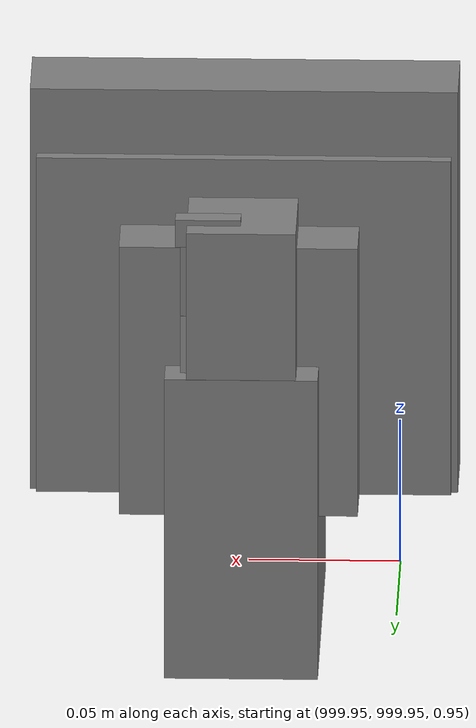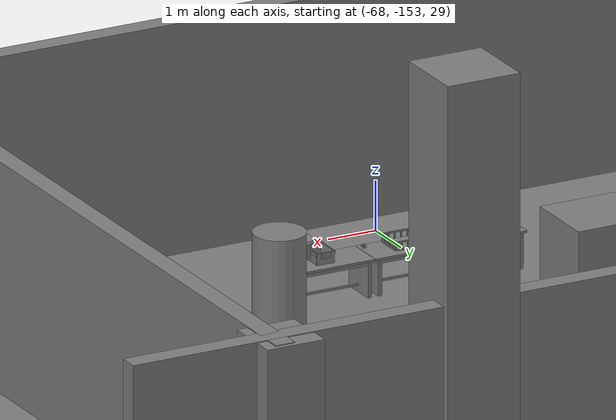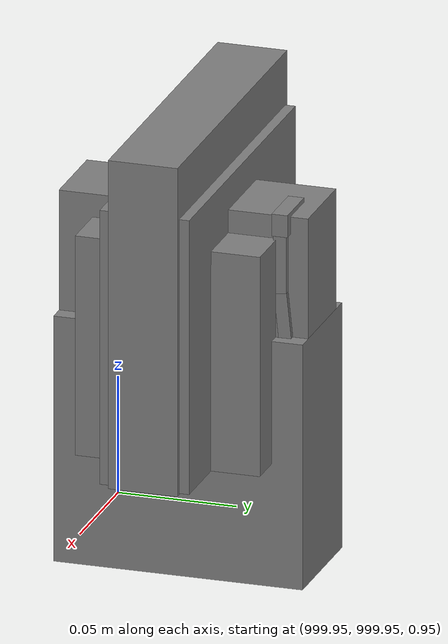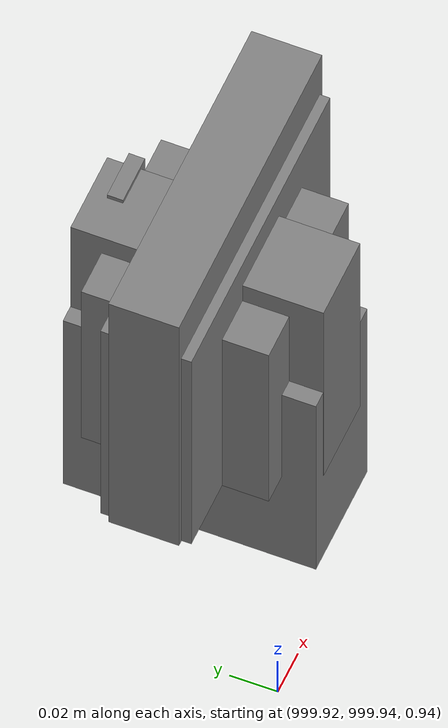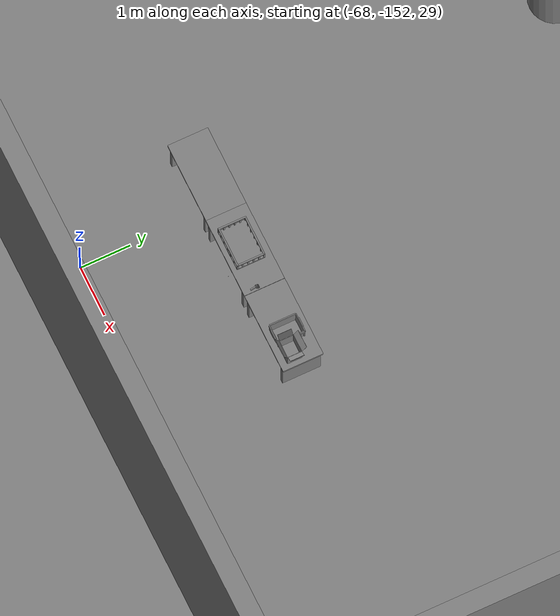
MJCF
<mujoco>
    <option gravity="0.000000000 0.000000000 -9.810000420" timestep="0.0049999999" integrator="implicitfast" density="1.225" viscosity="1.8000001e-05" noslip_iterations="10" iterations="100" sdf_iterations="50">
        <flag multiccd="disable"/>
    </option>
    <size memory="1000M"/>
    <compiler coordinate="local"/>
    <worldbody>
        <light cutoff="30" pos="0 1 1" dir="0 -1 -2"/>
        <light cutoff="30" pos="0 -1 1" dir="0 1 -2"/>
        <body pos="-64.866622925 -149.383972168 30.183746338" euler="89.999984741 89.999946594 0.000000000" name="openloong_gripper_2f85_fix_base_usda_bluebox_01">
            <geom contype="1" conaffinity="1" density="1000" type="box" material="" rgba="0.500000000 0.500000000 0.500000000 1.000000000" solimp="0.899999976 0.949999988 0.001000000" friction="1.000000000 0.005000000 0.000100000" solref="0.020000000 1.000000000" margin="0" condim="3" group="0" pos="0.276580811 0.187225342 0.000068665" quat="0.707106948 0.000077471 0.707106352 0.000077486" size="0.100000001 0.057999998 0.010000000" name="openloong_gripper_2f85_fix_base_usda_geom_732543AD_BF17_46AD_8D56_6758D12A58F6"/>
            <geom contype="1" conaffinity="1" density="1000" type="box" material="" rgba="0.500000000 0.500000000 0.500000000 1.000000000" solimp="0.899999976 0.949999988 0.001000000" friction="1.000000000 0.005000000 0.000100000" solref="0.020000000 1.000000000" margin="0" condim="3" group="0" pos="0.000000000 0.002883911 0.000000000" quat="0.999999881 0.000000000 0.000000000 0.000000000" size="0.254000008 0.003000000 0.172000006" name="openloong_gripper_2f85_fix_base_usda_geom_0DE81B9E_3680_41E2_A3DD_413CAD44740B"/>
            <geom contype="1" conaffinity="1" density="1000" type="box" material="" rgba="0.500000000 0.500000000 0.500000000 1.000000000" solimp="0.899999976 0.949999988 0.001000000" friction="1.000000000 0.005000000 0.000100000" solref="0.020000000 1.000000000" margin="0" condim="3" group="0" pos="0.000000000 0.124874115 0.173484802" quat="0.999796331 0.020176515 -0.000000015 0.000000030" size="0.259999990 0.119999997 0.007000000" name="openloong_gripper_2f85_fix_base_usda_geom_F008245B_0353_43CB_B50C_D1C08C7225AA"/>
            <geom contype="1" conaffinity="1" density="1000" type="box" material="" rgba="0.500000000 0.500000000 0.500000000 1.000000000" solimp="0.899999976 0.949999988 0.001000000" friction="1.000000000 0.005000000 0.000100000" solref="0.020000000 1.000000000" margin="0" condim="3" group="0" pos="0.000000000 0.124874115 -0.173469543" quat="0.999796331 -0.020176545 -0.000000015 0.000000000" size="0.259999990 0.119999997 0.007000000" name="openloong_gripper_2f85_fix_base_usda_geom_3C8C1107_545F_4F09_B5F4_645312D293BC"/>
            <geom contype="1" conaffinity="1" density="1000" type="box" material="" rgba="0.500000000 0.500000000 0.500000000 1.000000000" solimp="0.899999976 0.949999988 0.001000000" friction="1.000000000 0.005000000 0.000100000" solref="0.020000000 1.000000000" margin="0" condim="3" group="0" pos="0.000000000 0.214008331 0.188980103" quat="0.999912977 0.013176724 0.000000015 0.000000000" size="0.259999990 0.029999999 0.012500000" name="openloong_gripper_2f85_fix_base_usda_geom_BBC712BF_010A_4697_9E40_D23D85E93ACA"/>
            <geom contype="1" conaffinity="1" density="1000" type="box" material="" rgba="0.500000000 0.500000000 0.500000000 1.000000000" solimp="0.899999976 0.949999988 0.001000000" friction="1.000000000 0.005000000 0.000100000" solref="0.020000000 1.000000000" margin="0" condim="3" group="0" pos="-0.258361816 0.125289917 0.001876831" quat="0.702796936 -0.020792112 0.710783124 0.020769298" size="0.189999998 0.119999997 0.009000000" name="openloong_gripper_2f85_fix_base_usda_geom_491D5265_A027_4290_9C21_1770E2BD3424"/>
            <geom contype="1" conaffinity="1" density="1000" type="box" material="" rgba="0.500000000 0.500000000 0.500000000 1.000000000" solimp="0.899999976 0.949999988 0.001000000" friction="1.000000000 0.005000000 0.000100000" solref="0.020000000 1.000000000" margin="0" condim="3" group="0" pos="0.000000000 0.214008331 -0.188980103" quat="0.999912977 -0.013176769 0.000000030 0.000000015" size="0.259999990 0.029999999 0.012500000" name="openloong_gripper_2f85_fix_base_usda_geom_F37DC2E3_EF15_45DE_BCBF_43A69FA492F6"/>
            <geom contype="1" conaffinity="1" density="1000" type="box" material="" rgba="0.500000000 0.500000000 0.500000000 1.000000000" solimp="0.899999976 0.949999988 0.001000000" friction="1.000000000 0.005000000 0.000100000" solref="0.020000000 1.000000000" margin="0" condim="3" group="0" pos="-0.276611328 0.187225342 0.000068665" quat="0.707106650 0.000077441 0.707106709 0.000077456" size="0.100000001 0.057999998 0.010000000" name="openloong_gripper_2f85_fix_base_usda_geom_9C16E34C_BF21_4401_B389_94DEAC704061"/>
            <geom contype="1" conaffinity="1" density="1000" type="box" material="" rgba="0.500000000 0.500000000 0.500000000 1.000000000" solimp="0.899999976 0.949999988 0.001000000" friction="1.000000000 0.005000000 0.000100000" solref="0.020000000 1.000000000" margin="0" condim="3" group="0" pos="0.258331299 0.125289917 0.001876831" quat="0.702851415 0.018856421 0.710823774 -0.019329369" size="0.189999998 0.119999997 0.009000000" name="openloong_gripper_2f85_fix_base_usda_geom_E428DF02_E461_4A58_B05D_25E01E7C2E7A"/>
            <freejoint name="openloong_gripper_2f85_fix_base_usda_bluebox_01_joint"/>
            <site size="0.005000000 0.005000000 0.005000000" rgba="0.500000000 0.500000000 0.500000000 1.000000000" pos="0.000000000 0.000000000 0.000000000" quat="0.999961913 0.008726534 0.000000000 0.000000000" group="0" type="sphere" name="openloong_gripper_2f85_fix_base_usda_bluebox_01site"/>
        </body>
        <body pos="-64.496299744 -149.491867065 30.235729218" euler="0.000000000 0.000000000 89.999946594" name="openloong_gripper_2f85_fix_base_usda_cardboardbox_01">
            <geom contype="1" conaffinity="1" density="1000" type="box" material="" rgba="0.500000000 0.500000000 0.500000000 1.000000000" solimp="0.899999976 0.949999988 0.001000000" friction="1.000000000 0.005000000 0.000100000" solref="0.020000000 1.000000000" margin="0" condim="3" group="0" pos="-0.003166199 -0.004086494 0.005052090" quat="1.000000000 0.000000000 0.000000000 0.000000000" size="0.142499998 0.177500010 0.005000000" name="openloong_gripper_2f85_fix_base_usda_geom_F6C583F7_C363_45D2_BAF8_A6DE4DA166E1"/>
            <geom contype="1" conaffinity="1" density="1000" type="box" material="" rgba="0.500000000 0.500000000 0.500000000 1.000000000" solimp="0.899999976 0.949999988 0.001000000" friction="1.000000000 0.005000000 0.000100000" solref="0.020000000 1.000000000" margin="0" condim="3" group="0" pos="-0.003166199 0.170316696 0.150570869" quat="1.000000000 0.000000000 0.000000000 0.000000000" size="0.142499998 0.005000000 0.149999991" name="openloong_gripper_2f85_fix_base_usda_geom_9B9AF9D1_24B9_4E5E_AD23_6C0E00E91194"/>
            <geom contype="1" conaffinity="1" density="1000" type="box" material="" rgba="0.500000000 0.500000000 0.500000000 1.000000000" solimp="0.899999976 0.949999988 0.001000000" friction="1.000000000 0.005000000 0.000100000" solref="0.020000000 1.000000000" margin="0" condim="3" group="0" pos="-0.147399902 -0.005307198 0.150570869" quat="1.000000000 0.000000000 0.000000000 0.000000000" size="0.005000000 0.177500010 0.149999991" name="openloong_gripper_2f85_fix_base_usda_geom_BF38005D_6ACE_4318_9A09_EE60A68EA02C"/>
            <geom contype="1" conaffinity="1" density="1000" type="box" material="" rgba="0.500000000 0.500000000 0.500000000 1.000000000" solimp="0.899999976 0.949999988 0.001000000" friction="1.000000000 0.005000000 0.000100000" solref="0.020000000 1.000000000" margin="0" condim="3" group="0" pos="0.140275955 -0.005307198 0.150570869" quat="1.000000000 0.000000000 0.000000000 0.000000000" size="0.005000000 0.177500010 0.149999991" name="openloong_gripper_2f85_fix_base_usda_geom_D9868ECF_5068_456D_8DDD_08D9C5A63048"/>
            <geom contype="1" conaffinity="1" density="1000" type="box" material="" rgba="0.500000000 0.500000000 0.500000000 1.000000000" solimp="0.899999976 0.949999988 0.001000000" friction="1.000000000 0.005000000 0.000100000" solref="0.020000000 1.000000000" margin="0" condim="3" group="0" pos="-0.003166199 -0.181550980 0.150570869" quat="1.000000000 0.000000000 0.000000000 0.000000000" size="0.142499998 0.005000000 0.149999991" name="openloong_gripper_2f85_fix_base_usda_geom_0CFC7489_90C8_4F59_BAAD_8297ED8C9C85"/>
            <freejoint name="openloong_gripper_2f85_fix_base_usda_cardboardbox_01_joint"/>
            <site size="0.005000000 0.005000000 0.005000000" rgba="0.500000000 0.500000000 0.500000000 1.000000000" pos="0.000000000 0.000000000 0.000000000" quat="0.999961913 0.008726535 0.000000000 0.000000000" group="0" type="sphere" name="openloong_gripper_2f85_fix_base_usda_site_068F7B95_1200_4DAB_A1D6_D562FDFF64B6"/>
            <body pos="0.139160156 -0.004048347 0.301930904" euler="-179.999954224 49.383502960 179.999954224" name="openloong_gripper_2f85_fix_base_usda_A1_006">
                <geom contype="1" conaffinity="1" density="1000" type="box" material="" rgba="0.500000000 0.500000000 0.500000000 1.000000000" solimp="0.899999976 0.949999988 0.001000000" friction="1.000000000 0.005000000 0.000100000" solref="0.020000000 1.000000000" margin="0" condim="3" group="0" pos="-0.071587563 0.000009537 0.001745224" quat="0.999999881 0.000000000 0.000000000 0.000000000" size="0.071249999 0.179999992 0.002500000" name="openloong_gripper_2f85_fix_base_usda_geom_A4618977_BA59_4AB2_B03D_17D2DD68DB35"/>
                <joint armature="0" stiffness="0.07" damping="0.0099999998" axis="0.000000 1.000000 0.000000" type="hinge" name="openloong_gripper_2f85_fix_base_usda_A1_006"/>
            </body>
            <body pos="-0.145902634 -0.004086494 0.301938057" euler="-180.000000000 -60.000011444 -180.000000000" name="openloong_gripper_2f85_fix_base_usda_A2_006">
                <geom contype="1" conaffinity="1" density="1000" type="box" material="" rgba="0.500000000 0.500000000 0.500000000 1.000000000" solimp="0.899999976 0.949999988 0.001000000" friction="1.000000000 0.005000000 0.000100000" solref="0.020000000 1.000000000" margin="0" condim="3" group="0" pos="0.071268082 0.000009537 0.002717972" quat="0.000002921 0.000000000 -0.000000030 0.999999881" size="0.071249999 0.179999992 0.002500000" name="openloong_gripper_2f85_fix_base_usda_geom_CE5F023B_8AC2_497C_9A08_7E22B9B0B591"/>
                <joint armature="0" stiffness="0.07" damping="0.0099999998" axis="0.000000 1.000000 0.000000" type="hinge" name="openloong_gripper_2f85_fix_base_usda_A2_006"/>
            </body>
            <body pos="-0.003385544 0.175991058 0.301930904" euler="-125.858116150 -0.000004561 0.000002331" name="openloong_gripper_2f85_fix_base_usda_B2_006">
                <geom contype="1" conaffinity="1" density="1000" type="box" material="" rgba="0.500000000 0.500000000 0.500000000 1.000000000" solimp="0.899999976 0.949999988 0.001000000" friction="1.000000000 0.005000000 0.000100000" solref="0.020000000 1.000000000" margin="0" condim="3" group="0" pos="0.000009537 -0.070939064 -0.002470016" quat="0.999614120 0.027776197 -0.000000015 0.000000030" size="0.137500003 0.064999998 0.005000000" name="openloong_gripper_2f85_fix_base_usda_geom_215D9583_F5B4_4D08_91D1_C105B2F8B252"/>
                <joint armature="0" stiffness="0.07" damping="0.0099999998" axis="1.000000 0.000000 0.000000" type="hinge" name="openloong_gripper_2f85_fix_base_usda_B2_006"/>
            </body>
            <body pos="-0.003385544 -0.184140205 0.301938057" euler="147.805557251 0.000000000 0.000000000" name="openloong_gripper_2f85_fix_base_usda_B1_006">
                <geom contype="1" conaffinity="1" density="1000" type="box" material="" rgba="0.500000000 0.500000000 0.500000000 1.000000000" solimp="0.899999976 0.949999988 0.001000000" friction="1.000000000 0.005000000 0.000100000" solref="0.020000000 1.000000000" margin="0" condim="3" group="0" pos="-0.000028610 0.070202351 -0.002703667" quat="0.999614179 -0.027776167 0.000000000 0.000000000" size="0.137500003 0.064999998 0.005000000" name="openloong_gripper_2f85_fix_base_usda_geom_963DE4A2_8038_4B9B_8C7E_4C0D9F0FF4BB"/>
                <joint armature="0" stiffness="0.07" damping="0.0099999998" axis="1.000000 0.000000 0.000000" type="hinge" name="openloong_gripper_2f85_fix_base_usda_B1_006"/>
            </body>
        </body>
        <body pos="-65.882858276 -149.481979370 30.229999542" euler="-64.487716675 0.000000000 0.000000000" name="openloong_gripper_2f85_fix_base_usda_Barcode">
            <geom contype="1" conaffinity="1" density="1000" type="box" material="" rgba="0.500000000 0.500000000 0.500000000 1.000000000" solimp="0.899999976 0.949999988 0.001000000" friction="1.000000000 0.005000000 0.000100000" solref="0.020000000 1.000000000" margin="0" condim="3" group="0" pos="0.000000000 0.013038635 0.001419067" quat="0.000000000 0.000000000 0.000000000 1.000000119" size="0.034000002 0.010000000 0.017999999" name="openloong_gripper_2f85_fix_base_usda_geom_C50035E8_9517_4EFE_AF8A_ACF4AE5909BE"/>
            <geom contype="1" conaffinity="1" density="1000" type="box" material="" rgba="0.500000000 0.500000000 0.500000000 1.000000000" solimp="0.899999976 0.949999988 0.001000000" friction="1.000000000 0.005000000 0.000100000" solref="0.020000000 1.000000000" margin="0" condim="3" group="0" pos="0.000000000 -0.035301208 -0.007095337" quat="0.000000000 0.000000000 -0.043619365 0.999048233" size="0.028999999 0.010000000 0.020000000" name="openloong_gripper_2f85_fix_base_usda_geom_E7D4D458_6DEA_4F62_9073_5035855C3139"/>
            <geom contype="1" conaffinity="1" density="1000" type="box" material="" rgba="0.500000000 0.500000000 0.500000000 1.000000000" solimp="0.899999976 0.949999988 0.001000000" friction="1.000000000 0.005000000 0.000100000" solref="0.020000000 1.000000000" margin="0" condim="3" group="0" pos="0.000000000 -0.043411255 -0.011749268" quat="0.922262907 0.386563420 0.000000000 0.000000000" size="0.026000001 0.010000000 0.020000000" name="openloong_gripper_2f85_fix_base_usda_geom_A27A0309_FCDB_4A25_BFDC_6D071299C9AF"/>
            <geom contype="1" conaffinity="1" density="1000" type="box" material="" rgba="0.500000000 0.500000000 0.500000000 1.000000000" solimp="0.899999976 0.949999988 0.001000000" friction="1.000000000 0.005000000 0.000100000" solref="0.020000000 1.000000000" margin="0" condim="3" group="0" pos="0.000000000 -0.016967773 -0.031860352" quat="0.000000000 0.000000000 0.000000000 1.000000119" size="0.008000000 0.010000000 0.013000000" name="openloong_gripper_2f85_fix_base_usda_geom_6A78B3D4_AE83_4508_95CD_3C39B683BA4D"/>
            <geom contype="1" conaffinity="1" density="1000" type="box" material="" rgba="0.500000000 0.500000000 0.500000000 1.000000000" solimp="0.899999976 0.949999988 0.001000000" friction="1.000000000 0.005000000 0.000100000" solref="0.020000000 1.000000000" margin="0" condim="3" group="0" pos="0.000000000 -0.001869202 0.000312805" quat="0.953716993 0.300705761 0.000000000 0.000000000" size="0.032000002 0.010000000 0.018999999" name="openloong_gripper_2f85_fix_base_usda_geom_52519B8E_EC66_4255_9152_665F750DEA4E"/>
            <geom contype="1" conaffinity="1" density="1000" type="box" material="" rgba="0.500000000 0.500000000 0.500000000 1.000000000" solimp="0.899999976 0.949999988 0.001000000" friction="1.000000000 0.005000000 0.000100000" solref="0.020000000 1.000000000" margin="0" condim="3" group="0" pos="0.000000000 -0.019531250 -0.003173828" quat="0.953716993 0.300705761 0.000000000 0.000000000" size="0.030999999 0.010000000 0.020000000" name="openloong_gripper_2f85_fix_base_usda_geom_7CCF2826_B1C9_4426_BA28_1361CEBFDAB2"/>
            <geom contype="1" conaffinity="1" density="1000" type="box" material="" rgba="0.500000000 0.500000000 0.500000000 1.000000000" solimp="0.899999976 0.949999988 0.001000000" friction="1.000000000 0.005000000 0.000100000" solref="0.020000000 1.000000000" margin="0" condim="3" group="0" pos="0.000000000 -0.035301208 -0.007095337" quat="0.953716993 0.300705761 0.000000000 0.000000000" size="0.028999999 0.010000000 0.020000000" name="openloong_gripper_2f85_fix_base_usda_geom_B5BE3825_9255_4CEF_95EC_5D932AB8683C"/>
            <geom contype="1" conaffinity="1" density="1000" type="box" material="" rgba="0.500000000 0.500000000 0.500000000 1.000000000" solimp="0.899999976 0.949999988 0.001000000" friction="1.000000000 0.005000000 0.000100000" solref="0.020000000 1.000000000" margin="0" condim="3" group="0" pos="0.000000000 -0.042617798 -0.071121216" quat="0.000000000 0.000000000 0.000000000 1.000000119" size="0.013000000 0.021000000 0.059999999" name="openloong_gripper_2f85_fix_base_usda_geom_3296B6A4_0755_4BD4_91FD_AB582770A35D"/>
            <freejoint name="openloong_gripper_2f85_fix_base_usda_Barcode_joint"/>
            <site size="0.005000000 0.005000000 0.005000000" rgba="0.500000000 0.500000000 0.500000000 1.000000000" pos="0.000000000 0.000000000 0.000000000" quat="1.000000000 0.000000000 0.000000000 0.000000000" group="0" type="sphere" name="openloong_gripper_2f85_fix_base_usda_Barcode_site"/>
        </body>
        <body pos="-66.745018005 -149.392349243 30.184000015" euler="0.000000000 0.000000000 89.999946594" name="[22330464793038]_Basket_01">
            <geom contype="1" conaffinity="1" density="1000" type="box" material="" rgba="0.500000000 0.500000000 0.500000000 1.000000000" solimp="0.899999976 0.949999988 0.001000000" friction="1.000000000 0.005000000 0.000100000" solref="0.020000000 1.000000000" margin="0" condim="3" group="0" pos="-0.052425385 0.389207840 0.089787483" quat="0.707107008 0.000000000 0.000000000 0.707106411" size="0.014249999 0.014249999 0.059999999" name="[22330464793038]_geom_F34FC68B_F78D_44A7_B875_766B3B8A980D"/>
            <geom contype="1" conaffinity="1" density="1000" type="box" material="" rgba="0.500000000 0.500000000 0.500000000 1.000000000" solimp="0.899999976 0.949999988 0.001000000" friction="1.000000000 0.005000000 0.000100000" solref="0.020000000 1.000000000" margin="0" condim="3" group="0" pos="0.264015198 -0.133043289 0.089787483" quat="0.707107008 0.000000000 0.000000000 0.707106411" size="0.014249999 0.014249999 0.059999999" name="[22330464793038]_geom_CF690D19_159A_45C5_9861_F4D543F31A7E"/>
            <geom contype="1" conaffinity="1" density="1000" type="box" material="" rgba="0.500000000 0.500000000 0.500000000 1.000000000" solimp="0.899999976 0.949999988 0.001000000" friction="1.000000000 0.005000000 0.000100000" solref="0.020000000 1.000000000" margin="0" condim="3" group="0" pos="-0.264015198 -0.265548706 0.089793205" quat="0.707107008 0.000000000 0.000000000 0.707106411" size="0.014249999 0.014249999 0.059999999" name="[22330464793038]_geom_E6F491C2_0C1C_46C7_A754_231E9D003ADB"/>
            <geom contype="1" conaffinity="1" density="1000" type="box" material="" rgba="0.500000000 0.500000000 0.500000000 1.000000000" solimp="0.899999976 0.949999988 0.001000000" friction="1.000000000 0.005000000 0.000100000" solref="0.020000000 1.000000000" margin="0" condim="3" group="0" pos="-0.160263062 -0.389322281 0.089793205" quat="0.707107008 0.000000000 0.000000000 0.707106411" size="0.014249999 0.014249999 0.059999999" name="[22330464793038]_geom_10070406_3200_4F7C_B30B_74A445DD1414"/>
            <geom contype="1" conaffinity="1" density="1000" type="box" material="" rgba="0.500000000 0.500000000 0.500000000 1.000000000" solimp="0.899999976 0.949999988 0.001000000" friction="1.000000000 0.005000000 0.000100000" solref="0.020000000 1.000000000" margin="0" condim="3" group="0" pos="0.162265778 -0.389322281 0.089787483" quat="0.707107008 0.000000000 0.000000000 0.707106411" size="0.014249999 0.014249999 0.059999999" name="[22330464793038]_geom_237FE6AF_ACB7_4C6F_97A3_7A7061113986"/>
            <geom contype="1" conaffinity="1" density="1000" type="box" material="" rgba="0.500000000 0.500000000 0.500000000 1.000000000" solimp="0.899999976 0.949999988 0.001000000" friction="1.000000000 0.005000000 0.000100000" solref="0.020000000 1.000000000" margin="0" condim="3" group="0" pos="0.264015198 0.389207840 0.089787483" quat="0.707107008 0.000000000 0.000000000 0.707106411" size="0.014249999 0.014249999 0.059999999" name="[22330464793038]_geom_DDBA44C0_DF78_4AC9_B695_1A5C2B24543A"/>
            <geom contype="1" conaffinity="1" density="1000" type="box" material="" rgba="0.500000000 0.500000000 0.500000000 1.000000000" solimp="0.899999976 0.949999988 0.001000000" friction="1.000000000 0.005000000 0.000100000" solref="0.020000000 1.000000000" margin="0" condim="3" group="0" pos="-0.264015198 -0.133043289 0.089793205" quat="0.707107008 0.000000000 0.000000000 0.707106411" size="0.014249999 0.014249999 0.059999999" name="[22330464793038]_geom_DEBE16B1_7587_4266_8A7E_210E3B8C8A3A"/>
            <geom contype="1" conaffinity="1" density="1000" type="box" material="" rgba="0.500000000 0.500000000 0.500000000 1.000000000" solimp="0.899999976 0.949999988 0.001000000" friction="1.000000000 0.005000000 0.000100000" solref="0.020000000 1.000000000" margin="0" condim="3" group="0" pos="-0.264026642 0.269256592 0.089793205" quat="0.707107008 0.000000000 0.000000000 0.707106411" size="0.014249999 0.014249999 0.059999999" name="[22330464793038]_geom_ED86B005_4CC5_48E1_935A_076515F49F6B"/>
            <geom contype="1" conaffinity="1" density="1000" type="box" material="" rgba="0.500000000 0.500000000 0.500000000 1.000000000" solimp="0.899999976 0.949999988 0.001000000" friction="1.000000000 0.005000000 0.000100000" solref="0.020000000 1.000000000" margin="0" condim="3" group="0" pos="0.054462433 0.389207840 0.089787483" quat="0.707107008 0.000000000 0.000000000 0.707106411" size="0.014249999 0.014249999 0.059999999" name="[22330464793038]_geom_F6D7C35A_7655_480F_8BAB_2B355364F957"/>
            <geom contype="1" conaffinity="1" density="1000" type="box" material="" rgba="0.500000000 0.500000000 0.500000000 1.000000000" solimp="0.899999976 0.949999988 0.001000000" friction="1.000000000 0.005000000 0.000100000" solref="0.020000000 1.000000000" margin="0" condim="3" group="0" pos="0.054462433 -0.389322281 0.089787483" quat="0.707107008 0.000000000 0.000000000 0.707106411" size="0.014249999 0.014249999 0.059999999" name="[22330464793038]_geom_475688A2_6DAC_4E8E_A249_8B47AFB7FCB2"/>
            <geom contype="1" conaffinity="1" density="1000" type="box" material="" rgba="0.500000000 0.500000000 0.500000000 1.000000000" solimp="0.899999976 0.949999988 0.001000000" friction="1.000000000 0.005000000 0.000100000" solref="0.020000000 1.000000000" margin="0" condim="3" group="0" pos="0.264015198 0.269256592 0.089793205" quat="0.707107008 0.000000000 0.000000000 0.707106411" size="0.014249999 0.014249999 0.059999999" name="[22330464793038]_geom_522D5681_5490_4874_BB8E_A7ADBAB1A4B5"/>
            <geom contype="1" conaffinity="1" density="1000" type="box" material="" rgba="0.500000000 0.500000000 0.500000000 1.000000000" solimp="0.899999976 0.949999988 0.001000000" friction="1.000000000 0.005000000 0.000100000" solref="0.020000000 1.000000000" margin="0" condim="3" group="0" pos="0.264015198 -0.389322281 0.089787483" quat="0.707107008 0.000000000 0.000000000 0.707106411" size="0.014249999 0.014249999 0.059999999" name="[22330464793038]_geom_70ED64E7_BF96_4330_8D52_4C3A214708F5"/>
            <geom contype="1" conaffinity="1" density="1000" type="box" material="" rgba="0.500000000 0.500000000 0.500000000 1.000000000" solimp="0.899999976 0.949999988 0.001000000" friction="1.000000000 0.005000000 0.000100000" solref="0.020000000 1.000000000" margin="0" condim="3" group="0" pos="0.000000000 0.000000000 0.015998840" quat="0.707107008 0.000000000 0.000000000 0.707106411" size="0.403499991 0.279000014 0.015750000" name="[22330464793038]_geom_E59258F5_388F_473D_B4C4_7D8B321B66F8"/>
            <geom contype="1" conaffinity="1" density="1000" type="box" material="" rgba="0.500000000 0.500000000 0.500000000 1.000000000" solimp="0.899999976 0.949999988 0.001000000" friction="1.000000000 0.005000000 0.000100000" solref="0.020000000 1.000000000" margin="0" condim="3" group="0" pos="0.000000000 -0.389476776 0.163619041" quat="0.707107008 0.000000000 0.000000000 0.707106411" size="0.015000000 0.277500004 0.015750000" name="[22330464793038]_geom_69A464C6_9C71_4EDD_B6F1_2756EF752A8F"/>
            <geom contype="1" conaffinity="1" density="1000" type="box" material="" rgba="0.500000000 0.500000000 0.500000000 1.000000000" solimp="0.899999976 0.949999988 0.001000000" friction="1.000000000 0.005000000 0.000100000" solref="0.020000000 1.000000000" margin="0" condim="3" group="0" pos="0.162265778 0.389207840 0.089787483" quat="0.707107008 0.000000000 0.000000000 0.707106411" size="0.014249999 0.014249999 0.059999999" name="[22330464793038]_geom_E106EA8D_1559_449F_B040_CDC87BC5CA75"/>
            <geom contype="1" conaffinity="1" density="1000" type="box" material="" rgba="0.500000000 0.500000000 0.500000000 1.000000000" solimp="0.899999976 0.949999988 0.001000000" friction="1.000000000 0.005000000 0.000100000" solref="0.020000000 1.000000000" margin="0" condim="3" group="0" pos="0.000000000 0.389471054 0.163619041" quat="0.707107008 0.000000000 0.000000000 0.707106411" size="0.015000000 0.277500004 0.015750000" name="[22330464793038]_geom_1C7C3B82_EC06_4B14_B487_2173F380ABD2"/>
            <geom contype="1" conaffinity="1" density="1000" type="box" material="" rgba="0.500000000 0.500000000 0.500000000 1.000000000" solimp="0.899999976 0.949999988 0.001000000" friction="1.000000000 0.005000000 0.000100000" solref="0.020000000 1.000000000" margin="0" condim="3" group="0" pos="-0.263511658 0.000000000 0.163619041" quat="0.707107008 0.000000000 0.000000000 0.707106411" size="0.403499991 0.015000000 0.015750000" name="[22330464793038]_geom_8C3EC1EF_09E3_4DC9_84AC_E6D1D2BDAB3D"/>
            <geom contype="1" conaffinity="1" density="1000" type="box" material="" rgba="0.500000000 0.500000000 0.500000000 1.000000000" solimp="0.899999976 0.949999988 0.001000000" friction="1.000000000 0.005000000 0.000100000" solref="0.020000000 1.000000000" margin="0" condim="3" group="0" pos="-0.264015198 0.141334534 0.089793205" quat="0.707107008 0.000000000 0.000000000 0.707106411" size="0.014249999 0.014249999 0.059999999" name="[22330464793038]_geom_55FA75AC_7375_4EF5_A84A_6C7CE60289A0"/>
            <geom contype="1" conaffinity="1" density="1000" type="box" material="" rgba="0.500000000 0.500000000 0.500000000 1.000000000" solimp="0.899999976 0.949999988 0.001000000" friction="1.000000000 0.005000000 0.000100000" solref="0.020000000 1.000000000" margin="0" condim="3" group="0" pos="0.264015198 -0.265548706 0.089787483" quat="0.707107008 0.000000000 0.000000000 0.707106411" size="0.014249999 0.014249999 0.059999999" name="[22330464793038]_geom_CE226A35_BC0F_42C3_AE64_C13ED811E0F9"/>
            <geom contype="1" conaffinity="1" density="1000" type="box" material="" rgba="0.500000000 0.500000000 0.500000000 1.000000000" solimp="0.899999976 0.949999988 0.001000000" friction="1.000000000 0.005000000 0.000100000" solref="0.020000000 1.000000000" margin="0" condim="3" group="0" pos="-0.160263062 0.389207840 0.089787483" quat="0.707107008 0.000000000 0.000000000 0.707106411" size="0.014249999 0.014249999 0.059999999" name="[22330464793038]_geom_D90F22E2_9B68_4E50_A36C_A21B34772E3E"/>
            <geom contype="1" conaffinity="1" density="1000" type="box" material="" rgba="0.500000000 0.500000000 0.500000000 1.000000000" solimp="0.899999976 0.949999988 0.001000000" friction="1.000000000 0.005000000 0.000100000" solref="0.020000000 1.000000000" margin="0" condim="3" group="0" pos="-0.052425385 -0.389322281 0.089787483" quat="0.707107008 0.000000000 0.000000000 0.707106411" size="0.014249999 0.014249999 0.059999999" name="[22330464793038]_geom_ED67C432_B4BD_4253_AA2C_91F502575CC6"/>
            <geom contype="1" conaffinity="1" density="1000" type="box" material="" rgba="0.500000000 0.500000000 0.500000000 1.000000000" solimp="0.899999976 0.949999988 0.001000000" friction="1.000000000 0.005000000 0.000100000" solref="0.020000000 1.000000000" margin="0" condim="3" group="0" pos="-0.264026642 -0.389322281 0.089793205" quat="0.707107008 0.000000000 0.000000000 0.707106411" size="0.014249999 0.014249999 0.059999999" name="[22330464793038]_geom_F5882565_9FF6_488D_896E_1746B53D4BB9"/>
            <geom contype="1" conaffinity="1" density="1000" type="box" material="" rgba="0.500000000 0.500000000 0.500000000 1.000000000" solimp="0.899999976 0.949999988 0.001000000" friction="1.000000000 0.005000000 0.000100000" solref="0.020000000 1.000000000" margin="0" condim="3" group="0" pos="0.264015198 0.141334534 0.089787483" quat="0.707107008 0.000000000 0.000000000 0.707106411" size="0.014249999 0.014249999 0.059999999" name="[22330464793038]_geom_6C0C46D7_5D2E_412B_A0CA_3A50C983EDEC"/>
            <geom contype="1" conaffinity="1" density="1000" type="box" material="" rgba="0.500000000 0.500000000 0.500000000 1.000000000" solimp="0.899999976 0.949999988 0.001000000" friction="1.000000000 0.005000000 0.000100000" solref="0.020000000 1.000000000" margin="0" condim="3" group="0" pos="-0.264015198 0.389207840 0.089793205" quat="0.707107008 0.000000000 0.000000000 0.707106411" size="0.014249999 0.014249999 0.059999999" name="[22330464793038]_geom_6AC9AD81_B0AC_460D_9762_6459FBC8CCC9"/>
            <geom contype="1" conaffinity="1" density="1000" type="box" material="" rgba="0.500000000 0.500000000 0.500000000 1.000000000" solimp="0.899999976 0.949999988 0.001000000" friction="1.000000000 0.005000000 0.000100000" solref="0.020000000 1.000000000" margin="0" condim="3" group="0" pos="0.264015198 0.004480362 0.089787483" quat="0.707107008 0.000000000 0.000000000 0.707106411" size="0.014249999 0.014249999 0.059999999" name="[22330464793038]_geom_BDBEEEE4_A283_4FDD_8ABA_E390B974A9C9"/>
            <geom contype="1" conaffinity="1" density="1000" type="box" material="" rgba="0.500000000 0.500000000 0.500000000 1.000000000" solimp="0.899999976 0.949999988 0.001000000" friction="1.000000000 0.005000000 0.000100000" solref="0.020000000 1.000000000" margin="0" condim="3" group="0" pos="0.263694763 -0.000011444 0.163619041" quat="0.707107008 0.000000000 0.000000000 0.707106411" size="0.403499991 0.015000000 0.015750000" name="[22330464793038]_geom_41E9C65A_F1CB_4850_B069_45FFA47D04CA"/>
            <geom contype="1" conaffinity="1" density="1000" type="box" material="" rgba="0.500000000 0.500000000 0.500000000 1.000000000" solimp="0.899999976 0.949999988 0.001000000" friction="1.000000000 0.005000000 0.000100000" solref="0.020000000 1.000000000" margin="0" condim="3" group="0" pos="-0.264015198 0.004480362 0.089793205" quat="0.707107008 0.000000000 0.000000000 0.707106411" size="0.014249999 0.014249999 0.059999999" name="[22330464793038]_geom_5E512CB2_144C_4645_9874_ACD25AA8118D"/>
            <freejoint name="[22330464793038]_joint_1AA55A60_0438_4505_AA10_DC4BDBB413C5"/>
        </body>
        <body pos="0.000000000 0.000000000 0.000000000" euler="0.000000000 0.000000000 0.000000000" name="Static Objects_Static Objects">
            <geom contype="1" conaffinity="1" density="1000" type="box" material="" rgba="0.500000000 0.500000000 0.500000000 1.000000000" solimp="0.899999976 0.949999988 0.001000000" friction="1.000000000 0.005000000 0.000100000" solref="0.020000000 1.000000000" margin="0" condim="3" group="0" pos="-67.544113159 -149.365814209 29.727830887" quat="0.500000417 0.499999970 0.499999553 0.499999970" size="0.381000012 0.319999993 0.041000001" name="Static Objects_geom_2F3BA286_07A8_4D81_BC38_2B9ED070B731"/>
            <geom contype="1" conaffinity="1" density="1000" type="box" material="" rgba="0.500000000 0.500000000 0.500000000 1.000000000" solimp="0.899999976 0.949999988 0.001000000" friction="1.000000000 0.005000000 0.000100000" solref="0.020000000 1.000000000" margin="0" condim="3" group="0" pos="-68.239501953 -149.365814209 30.086868286" quat="0.500000417 0.499999970 0.499999553 0.499999970" size="0.370999992 0.039500002 0.745000005" name="Static Objects_geom_4A056888_00EA_4E74_962D_AD34477F7396"/>
            <geom contype="1" conaffinity="1" density="1000" type="box" material="" rgba="0.500000000 0.500000000 0.500000000 1.000000000" solimp="0.899999976 0.949999988 0.001000000" friction="1.000000000 0.005000000 0.000100000" solref="0.020000000 1.000000000" margin="0" condim="3" group="0" pos="-68.239501953 -149.365814209 30.147235870" quat="0.500000417 0.499999970 0.499999553 0.499999970" size="0.400000006 0.022000000 0.800000012" name="Static Objects_geom_EEB42142_73F8_48FA_92D0_B0EA294C19B2"/>
            <geom contype="1" conaffinity="1" density="1000" type="box" material="" rgba="0.500000000 0.500000000 0.500000000 1.000000000" solimp="0.899999976 0.949999988 0.001000000" friction="1.000000000 0.005000000 0.000100000" solref="0.020000000 1.000000000" margin="0" condim="3" group="0" pos="-68.934890747 -149.365814209 29.727830887" quat="0.500000417 0.499999970 0.499999553 0.499999970" size="0.381000012 0.319999993 0.041000001" name="Static Objects_geom_7E6D3939_B4A4_4C67_AE2C_1804CE12195C"/>
            <geom contype="1" conaffinity="1" density="1000" type="box" material="" rgba="0.500000000 0.500000000 0.500000000 1.000000000" solimp="0.899999976 0.949999988 0.001000000" friction="1.000000000 0.005000000 0.000100000" solref="0.020000000 1.000000000" margin="0" condim="3" group="0" pos="-68.239501953 -149.365814209 29.561563492" quat="0.500000417 0.499999970 0.499999553 0.499999970" size="0.020000000 0.022000000 0.660000026" name="Static Objects_geom_78AFBF07_D7DD_42BF_9C72_41117F6F7555"/>
            <geom contype="1" conaffinity="1" density="1000" type="box" material="" rgba="0.500000000 0.500000000 0.500000000 1.000000000" solimp="0.899999976 0.949999988 0.001000000" friction="1.000000000 0.005000000 0.000100000" solref="0.020000000 1.000000000" margin="0" condim="3" group="0" pos="-65.945671082 -149.365814209 29.727830887" quat="0.500000417 0.499999970 0.499999553 0.499999970" size="0.381000012 0.319999993 0.041000001" name="Static Objects_geom_61FCCB04_DD33_4F34_A425_50751762BF8A"/>
            <geom contype="1" conaffinity="1" density="1000" type="box" material="" rgba="0.500000000 0.500000000 0.500000000 1.000000000" solimp="0.899999976 0.949999988 0.001000000" friction="1.000000000 0.005000000 0.000100000" solref="0.020000000 1.000000000" margin="0" condim="3" group="0" pos="-66.641059875 -149.365814209 30.086868286" quat="0.500000417 0.499999970 0.499999553 0.499999970" size="0.370999992 0.039500002 0.745000005" name="Static Objects_geom_E4938738_7F39_4927_A00C_3649D0AA6B83"/>
            <geom contype="1" conaffinity="1" density="1000" type="box" material="" rgba="0.500000000 0.500000000 0.500000000 1.000000000" solimp="0.899999976 0.949999988 0.001000000" friction="1.000000000 0.005000000 0.000100000" solref="0.020000000 1.000000000" margin="0" condim="3" group="0" pos="-66.641059875 -149.365814209 30.147235870" quat="0.500000417 0.499999970 0.499999553 0.499999970" size="0.400000006 0.022000000 0.800000012" name="Static Objects_geom_65C24100_018C_4CCF_BA7B_74C078BFFF3A"/>
            <geom contype="1" conaffinity="1" density="1000" type="box" material="" rgba="0.500000000 0.500000000 0.500000000 1.000000000" solimp="0.899999976 0.949999988 0.001000000" friction="1.000000000 0.005000000 0.000100000" solref="0.020000000 1.000000000" margin="0" condim="3" group="0" pos="-67.336448669 -149.365814209 29.727830887" quat="0.500000417 0.499999970 0.499999553 0.499999970" size="0.381000012 0.319999993 0.041000001" name="Static Objects_geom_B54869CB_D629_41C3_AE2E_33B6C2D1E3DD"/>
            <geom contype="1" conaffinity="1" density="1000" type="box" material="" rgba="0.500000000 0.500000000 0.500000000 1.000000000" solimp="0.899999976 0.949999988 0.001000000" friction="1.000000000 0.005000000 0.000100000" solref="0.020000000 1.000000000" margin="0" condim="3" group="0" pos="-66.641059875 -149.365814209 29.561563492" quat="0.500000417 0.499999970 0.499999553 0.499999970" size="0.020000000 0.022000000 0.660000026" name="Static Objects_geom_489E61C0_D623_467A_9E87_6A266685E7B2"/>
            <geom contype="1" conaffinity="1" density="1000" type="box" material="" rgba="0.500000000 0.500000000 0.500000000 1.000000000" solimp="0.899999976 0.949999988 0.001000000" friction="1.000000000 0.005000000 0.000100000" solref="0.020000000 1.000000000" margin="0" condim="3" group="0" pos="-64.338577271 -149.365814209 29.727830887" quat="0.500000417 0.499999970 0.499999553 0.499999970" size="0.381000012 0.319999993 0.041000001" name="Static Objects_geom_930CBCBE_F2F7_4C38_8C75_898B69428289"/>
            <geom contype="1" conaffinity="1" density="1000" type="box" material="" rgba="0.500000000 0.500000000 0.500000000 1.000000000" solimp="0.899999976 0.949999988 0.001000000" friction="1.000000000 0.005000000 0.000100000" solref="0.020000000 1.000000000" margin="0" condim="3" group="0" pos="-65.033966064 -149.365814209 30.086868286" quat="0.500000417 0.499999970 0.499999553 0.499999970" size="0.370999992 0.039500002 0.745000005" name="Static Objects_geom_BB7FE3BC_0182_4D6D_B6CA_D52557691433"/>
            <geom contype="1" conaffinity="1" density="1000" type="box" material="" rgba="0.500000000 0.500000000 0.500000000 1.000000000" solimp="0.899999976 0.949999988 0.001000000" friction="1.000000000 0.005000000 0.000100000" solref="0.020000000 1.000000000" margin="0" condim="3" group="0" pos="-65.033966064 -149.365814209 30.147235870" quat="0.500000417 0.499999970 0.499999553 0.499999970" size="0.400000006 0.022000000 0.800000012" name="Static Objects_geom_D5DAAA07_54FA_4807_BF53_6793989C078B"/>
            <geom contype="1" conaffinity="1" density="1000" type="box" material="" rgba="0.500000000 0.500000000 0.500000000 1.000000000" solimp="0.899999976 0.949999988 0.001000000" friction="1.000000000 0.005000000 0.000100000" solref="0.020000000 1.000000000" margin="0" condim="3" group="0" pos="-65.729354858 -149.365814209 29.727830887" quat="0.500000417 0.499999970 0.499999553 0.499999970" size="0.381000012 0.319999993 0.041000001" name="Static Objects_geom_DF6F572B_1569_46FD_A501_73D4516CEF75"/>
            <geom contype="1" conaffinity="1" density="1000" type="box" material="" rgba="0.500000000 0.500000000 0.500000000 1.000000000" solimp="0.899999976 0.949999988 0.001000000" friction="1.000000000 0.005000000 0.000100000" solref="0.020000000 1.000000000" margin="0" condim="3" group="0" pos="-65.033966064 -149.365814209 29.561563492" quat="0.500000417 0.499999970 0.499999553 0.499999970" size="0.020000000 0.022000000 0.660000026" name="Static Objects_geom_5D077E7C_6243_4F15_9036_1EBF14FF30C0"/>
            <geom contype="1" conaffinity="1" density="1000" type="box" material="" rgba="0.500000000 0.500000000 0.500000000 1.000000000" solimp="0.899999976 0.949999988 0.001000000" friction="1.000000000 0.005000000 0.000100000" solref="0.020000000 1.000000000" margin="0" condim="3" group="0" pos="-61.754566193 -137.853729248 33.906845093" quat="0.707107067 0.000000000 0.000000000 0.707106471" size="0.759999990 0.759999990 4.500000000" name="Static Objects_geom_27569669_C3B5_4FFF_8515_7534C1369916"/>
            <geom contype="1" conaffinity="1" density="1000" type="box" material="" rgba="0.500000000 0.500000000 0.500000000 1.000000000" solimp="0.899999976 0.949999988 0.001000000" friction="1.000000000 0.005000000 0.000100000" solref="0.020000000 1.000000000" margin="0" condim="3" group="0" pos="-57.511135101 -144.927108765 31.707921982" quat="1.000000000 0.000000000 0.000000000 0.000000000" size="0.200000003 8.000000000 2.299999952" name="Static Objects_geom_472C9615_72CA_4226_A5D5_8A1A65428104"/>
            <geom contype="1" conaffinity="1" density="1000" type="box" material="" rgba="0.500000000 0.500000000 0.500000000 1.000000000" solimp="0.899999976 0.949999988 0.001000000" friction="1.000000000 0.005000000 0.000100000" solref="0.020000000 1.000000000" margin="0" condim="3" group="0" pos="-80.517646790 -157.574050903 31.688196182" quat="0.707107067 0.000000000 0.000000000 0.707106471" size="0.600000024 0.600000024 2.299999952" name="Static Objects_geom_26A9D35B_1F70_449D_AFE1_261354208634"/>
            <geom contype="1" conaffinity="1" density="1000" type="box" material="" rgba="0.500000000 0.500000000 0.500000000 1.000000000" solimp="0.899999976 0.949999988 0.001000000" friction="1.000000000 0.005000000 0.000100000" solref="0.020000000 1.000000000" margin="0" condim="3" group="0" pos="-80.711044312 -147.414932251 31.666158676" quat="1.000000000 0.000000000 0.000000000 0.000000000" size="0.200000003 10.000000000 2.299999952" name="Static Objects_geom_DF50E4D9_36FF_4805_AB53_7F2757F8652C"/>
            <geom contype="1" conaffinity="1" density="1000" type="box" material="" rgba="0.500000000 0.500000000 0.500000000 1.000000000" solimp="0.899999976 0.949999988 0.001000000" friction="1.000000000 0.005000000 0.000100000" solref="0.020000000 1.000000000" margin="0" condim="3" group="0" pos="-57.687217712 -137.434692383 31.688196182" quat="0.707107067 0.000000000 0.000000000 0.707106471" size="0.600000024 0.600000024 2.299999952" name="Static Objects_geom_9C2587DF_CB84_43A8_8E93_2F93AD775030"/>
            <geom contype="1" conaffinity="1" density="1000" type="box" material="" rgba="0.500000000 0.500000000 0.500000000 1.000000000" solimp="0.899999976 0.949999988 0.001000000" friction="1.000000000 0.005000000 0.000100000" solref="0.020000000 1.000000000" margin="0" condim="3" group="0" pos="-69.537033081 -140.263229370 31.714921951" quat="0.707107067 0.000000000 0.000000000 0.707106471" size="0.759999990 4.500000000 2.299999952" name="Static Objects_geom_DA7A3DC6_A15D_4FBF_830F_3F2B366ED1FA"/>
            <geom contype="1" conaffinity="1" density="1000" type="box" material="" rgba="0.500000000 0.500000000 0.500000000 1.000000000" solimp="0.899999976 0.949999988 0.001000000" friction="1.000000000 0.005000000 0.000100000" solref="0.020000000 1.000000000" margin="0" condim="3" group="0" pos="-80.073638916 -137.853713989 33.906845093" quat="0.707107067 0.000000000 0.000000000 0.707106471" size="0.759999990 0.759999990 4.500000000" name="Static Objects_geom_0BB2C17C_9C1A_4AFF_B1B1_970C4A5A1B7F"/>
            <geom contype="1" conaffinity="1" density="1000" type="box" material="" rgba="0.500000000 0.500000000 0.500000000 1.000000000" solimp="0.899999976 0.949999988 0.001000000" friction="1.000000000 0.005000000 0.000100000" solref="0.020000000 1.000000000" margin="0" condim="3" group="0" pos="-73.406707764 -155.734664917 31.707921982" quat="1.000000000 0.000000000 0.000000000 0.000000000" size="0.200000003 3.000000000 2.299999952" name="Static Objects_geom_8EB601E3_F80C_475F_90CE_CE6753D09C3B"/>
            <geom contype="1" conaffinity="1" density="1000" type="box" material="" rgba="0.500000000 0.500000000 0.500000000 1.000000000" solimp="0.899999976 0.949999988 0.001000000" friction="1.000000000 0.005000000 0.000100000" solref="0.020000000 1.000000000" margin="0" condim="3" group="0" pos="-68.497543335 -137.448257446 31.707921982" quat="0.707107067 0.000000000 0.000000000 0.707106471" size="0.200000003 14.000000000 2.299999952" name="Static Objects_geom_B3902F11_D09B_4844_B1D7_CE3864E63205"/>
            <geom contype="1" conaffinity="1" density="1000" type="cylinder" material="" rgba="0.500000000 0.500000000 0.500000000 1.000000000" solimp="0.899999976 0.949999988 0.001000000" friction="1.000000000 0.005000000 0.000100000" solref="0.020000000 1.000000000" margin="0" condim="3" group="0" pos="-68.868522644 -142.134506226 31.711090088" quat="0.707107067 0.000000000 0.000000000 0.707106471" size="0.509999990 2.299999952 1.000000000" name="Static Objects_geom_2E75C0A8_9E94_4DA9_8F62_4A2822EFB75F"/>
            <geom contype="1" conaffinity="1" density="1000" type="plane" material="" rgba="0.500000000 0.500000000 0.500000000 1.000000000" solimp="0.899999976 0.949999988 0.001000000" friction="1.000000000 0.005000000 0.000100000" solref="0.020000000 1.000000000" margin="0" condim="3" group="0" pos="-72.873703003 -147.131927490 29.409669876" quat="1.000000000 0.000000000 0.000000000 0.000000000" size="18.000000000 14.000000000 1.000000000" name="Static Objects_geom_C79CE48A_CEDA_406D_9F1E_A69DE8DF1DB0"/>
            <geom contype="1" conaffinity="1" density="1000" type="box" material="" rgba="0.500000000 0.500000000 0.500000000 1.000000000" solimp="0.899999976 0.949999988 0.001000000" friction="1.000000000 0.005000000 0.000100000" solref="0.020000000 1.000000000" margin="0" condim="3" group="0" pos="-79.943580627 -157.782272339 31.707921982" quat="0.707107067 0.000000000 0.000000000 0.707106471" size="0.200000003 7.000000000 2.299999952" name="Static Objects_geom_6CCDD7C5_431E_4762_B5C4_EDF46E6323E5"/>
            <geom contype="1" conaffinity="1" density="1000" type="box" material="" rgba="0.500000000 0.500000000 0.500000000 1.000000000" solimp="0.899999976 0.949999988 0.001000000" friction="1.000000000 0.005000000 0.000100000" solref="0.020000000 1.000000000" margin="0" condim="3" group="0" pos="-65.421028137 -152.903442383 31.707921982" quat="0.707107067 0.000000000 0.000000000 0.707106471" size="0.200000003 7.800000191 2.299999952" name="Static Objects_geom_132A0E65_0FDD_424A_BA73_1DCE71F3F7AE"/>
            <geom contype="1" conaffinity="1" density="1000" type="box" material="" rgba="0.500000000 0.500000000 0.500000000 1.000000000" solimp="0.899999976 0.949999988 0.001000000" friction="1.000000000 0.005000000 0.000100000" solref="0.020000000 1.000000000" margin="0" condim="3" group="0" pos="-74.776908875 -149.964416504 31.688196182" quat="1.000000000 0.000000000 0.000000000 0.000000000" size="0.600000024 0.409999996 2.299999952" name="Static Objects_geom_C8A62A0B_2EAA_486A_9B15_5555C523042F"/>
            <geom contype="1" conaffinity="1" density="1000" type="cylinder" material="" rgba="0.500000000 0.500000000 0.500000000 1.000000000" solimp="0.899999976 0.949999988 0.001000000" friction="1.000000000 0.005000000 0.000100000" solref="0.020000000 1.000000000" margin="0" condim="3" group="0" pos="-60.161884308 -142.134506226 31.711090088" quat="0.707107067 0.000000000 0.000000000 0.707106471" size="0.509999990 2.299999952 1.000000000" name="Static Objects_geom_DB40F20C_C7B9_409F_863D_5CC27C45A06B"/>
            <geom contype="1" conaffinity="1" density="1000" type="cylinder" material="" rgba="0.500000000 0.500000000 0.500000000 1.000000000" solimp="0.899999976 0.949999988 0.001000000" friction="1.000000000 0.005000000 0.000100000" solref="0.020000000 1.000000000" margin="0" condim="3" group="0" pos="-75.382453918 -149.963455200 31.711090088" quat="0.707107067 0.000000000 0.000000000 0.707106471" size="0.409999996 2.299999952 1.000000000" name="Static Objects_geom_4AEE5B67_B725_48E0_AE47_DA778C93F444"/>
            <geom contype="1" conaffinity="1" density="1000" type="cylinder" material="" rgba="0.500000000 0.500000000 0.500000000 1.000000000" solimp="0.899999976 0.949999988 0.001000000" friction="1.000000000 0.005000000 0.000100000" solref="0.020000000 1.000000000" margin="0" condim="3" group="0" pos="-74.154960632 -149.963455200 31.711090088" quat="0.707107067 0.000000000 0.000000000 0.707106471" size="0.409999996 2.299999952 1.000000000" name="Static Objects_geom_B099AC08_FE1E_4807_88DC_9CEDCDB151B2"/>
            <geom contype="1" conaffinity="1" density="1000" type="cylinder" material="" rgba="0.500000000 0.500000000 0.500000000 1.000000000" solimp="0.899999976 0.949999988 0.001000000" friction="1.000000000 0.005000000 0.000100000" solref="0.020000000 1.000000000" margin="0" condim="3" group="0" pos="-77.566612244 -142.134506226 31.711090088" quat="0.707107067 0.000000000 0.000000000 0.707106471" size="0.509999990 2.299999952 1.000000000" name="Static Objects_geom_A7B75EBE_5A27_4879_9FE5_3E9C378750E9"/>
        </body>
        <body pos="1000.000000000 1000.000000000 1.000000000" euler="0.000000000 0.000000000 180.000000000" name="openloong_gripper_2f85_fix_base_usda_cpu_fan">
            <geom contype="1" conaffinity="1" density="1000" type="box" material="" rgba="0.500000000 0.500000000 0.500000000 1.000000000" solimp="0.899999976 0.949999988 0.001000000" friction="1.000000000 0.005000000 0.000100000" solref="0.020000000 1.000000000" margin="0" condim="3" group="0" pos="0.000000000 0.000000000 0.070034981" quat="0.000000000 0.000000000 0.000000000 1.000000000" size="0.070700005 0.014699999 0.070700005" name="openloong_gripper_2f85_fix_base_usda_geom_15FCCFAA_BC94_48DD_825D_21F6F15166D6"/>
            <freejoint name="openloong_gripper_2f85_fix_base_usda_cpu_fan_joint"/>
            <site size="0.005000000 0.005000000 0.005000000" rgba="0.500000000 0.500000000 0.500000000 1.000000000" pos="0.000000000 0.000000000 0.000000000" quat="0.999961913 0.008726535 0.000000000 0.000000000" group="0" type="sphere" name="openloong_gripper_2f85_fix_base_usda_cpu_fancsite"/>
        </body>
        <body pos="-65.926101685 -149.306427002 31.167619705" euler="-158.048461914 -40.392875671 -117.936241150" mocap="true" name="spotlight3_SpotLight"/>
        <body pos="1000.000000000 1000.000000000 1.000000000" euler="0.000000000 0.000000000 180.000000000" name="openloong_gripper_2f85_fix_base_usda_battery_01">
            <geom contype="1" conaffinity="1" density="1000" type="box" material="" rgba="0.500000000 0.500000000 0.500000000 1.000000000" solimp="0.899999976 0.949999988 0.001000000" friction="1.000000000 0.005000000 0.000100000" solref="0.020000000 1.000000000" margin="0" condim="3" group="0" pos="-0.011123657 -0.041940309 0.101691343" quat="1.000000000 0.000000000 0.000000000 0.000000000" size="0.010800000 0.003375000 0.004725000" name="openloong_gripper_2f85_fix_base_usda_geom_A8BD6028_D34F_47EC_BC4E_75BEA66306E9"/>
            <geom contype="1" conaffinity="1" density="1000" type="box" material="" rgba="0.500000000 0.500000000 0.500000000 1.000000000" solimp="0.899999976 0.949999988 0.001000000" friction="1.000000000 0.005000000 0.000100000" solref="0.020000000 1.000000000" margin="0" condim="3" group="0" pos="-0.010876465 -0.044247437 0.047066893" quat="0.998702705 -0.050920475 0.000000000 0.000000000" size="0.009450001 0.002700000 0.024975000" name="openloong_gripper_2f85_fix_base_usda_geom_43CBA10A_FDD7_423C_9B61_C33E4F98DEC2"/>
            <geom contype="1" conaffinity="1" density="1000" type="box" material="" rgba="0.500000000 0.500000000 0.500000000 1.000000000" solimp="0.899999976 0.949999988 0.001000000" friction="1.000000000 0.005000000 0.000100000" solref="0.020000000 1.000000000" margin="0" condim="3" group="0" pos="-0.001235962 -0.000659180 0.047381196" quat="1.000000000 0.000000000 0.000000000 0.000000000" size="0.039420001 0.039150000 0.047250003" name="openloong_gripper_2f85_fix_base_usda_geom_79143CC9_7700_47B5_9251_63F7E6D35679"/>
            <geom contype="1" conaffinity="1" density="1000" type="box" material="" rgba="0.500000000 0.500000000 0.500000000 1.000000000" solimp="0.899999976 0.949999988 0.001000000" friction="1.000000000 0.005000000 0.000100000" solref="0.020000000 1.000000000" margin="0" condim="3" group="0" pos="-0.010876465 -0.039138794 0.009851727" quat="1.000000000 0.000000000 0.000000000 0.000000000" size="0.009450001 0.010800000 0.013500000" name="openloong_gripper_2f85_fix_base_usda_geom_48C4984D_B9A7_404B_8B06_4C96031FB0E1"/>
            <geom contype="1" conaffinity="1" density="1000" type="box" material="" rgba="0.500000000 0.500000000 0.500000000 1.000000000" solimp="0.899999976 0.949999988 0.001000000" friction="1.000000000 0.005000000 0.000100000" solref="0.020000000 1.000000000" margin="0" condim="3" group="0" pos="-0.010876465 -0.041528322 0.071508206" quat="1.000000000 0.000000000 0.000000000 0.000000000" size="0.009450001 0.002700000 0.027000001" name="openloong_gripper_2f85_fix_base_usda_geom_D8A4633C_3036_41D4_A803_BB1404DDA96F"/>
            <freejoint name="openloong_gripper_2f85_fix_base_usda_battery_01_joint"/>
            <site size="0.005000000 0.005000000 0.005000000" rgba="0.500000000 0.500000000 0.500000000 1.000000000" pos="0.000000000 0.000000000 0.000000000" quat="0.999961913 0.008726500 0.000000000 0.000000000" group="0" type="sphere" name="openloong_gripper_2f85_fix_base_usda_battery_01site"/>
        </body>
        <body pos="1000.000000000 1000.000000000 1.000000000" euler="0.000011953 0.000005123 -179.999984741" name="openloong_gripper_2f85_fix_base_usda_intel_box">
            <geom contype="1" conaffinity="1" density="1000" type="box" material="" rgba="0.500000000 0.500000000 0.500000000 1.000000000" solimp="0.899999976 0.949999988 0.001000000" friction="1.000000000 0.005000000 0.000100000" solref="0.020000000 1.000000000" margin="0" condim="3" group="0" pos="0.000000000 -0.000067139 0.000082284" quat="0.707106709 0.000000225 0.000000253 0.707106650" size="0.052800003 0.025300000 0.052800003" name="openloong_gripper_2f85_fix_base_usda_geom_5A8BB285_E9D2_4FE4_A8A9_5A8A0275FF03"/>
            <freejoint name="openloong_gripper_2f85_fix_base_usda_intel_box_joint"/>
            <site size="0.005000000 0.005000000 0.005000000" rgba="0.500000000 0.500000000 0.500000000 1.000000000" pos="0.000000000 0.000000000 0.000000000" quat="0.999961913 0.008726500 0.000000000 0.000000000" group="0" type="sphere" name="openloong_gripper_2f85_fix_base_usda_intel_boxsite"/>
        </body>
        <body pos="1000.000000000 1000.000000000 1.000000000" euler="0.000000000 0.000000000 180.000000000" name="openloong_gripper_2f85_fix_base_usda_wifi_box">
            <geom contype="1" conaffinity="1" density="1000" type="box" material="" rgba="0.500000000 0.500000000 0.500000000 1.000000000" solimp="0.899999976 0.949999988 0.001000000" friction="1.000000000 0.005000000 0.000100000" solref="0.020000000 1.000000000" margin="0" condim="3" group="0" pos="0.000000000 0.000000000 0.058978677" quat="0.000000000 0.000000047 0.000000000 1.000000000" size="0.068499997 0.018999999 0.059000000" name="openloong_gripper_2f85_fix_base_usda_geom_6A2BF3E8_60A6_45C9_BAF4_5B1E072A2012"/>
            <freejoint name="openloong_gripper_2f85_fix_base_usda_wifi_box_joint"/>
            <site size="0.005000000 0.005000000 0.005000000" rgba="0.500000000 0.500000000 0.500000000 1.000000000" pos="0.000000000 0.000000000 0.000000000" quat="0.999961913 0.008726500 0.000000000 0.000000000" group="0" type="sphere" name="openloong_gripper_2f85_fix_base_usda_wifi_boxsite"/>
        </body>
        <body pos="1000.000000000 999.999938965 1.000000000" euler="0.000000000 0.000000000 180.000000000" name="openloong_gripper_2f85_fix_base_usda_intelcore_i5">
            <geom contype="1" conaffinity="1" density="1000" type="box" material="" rgba="0.500000000 0.500000000 0.500000000 1.000000000" solimp="0.899999976 0.949999988 0.001000000" friction="1.000000000 0.005000000 0.000100000" solref="0.020000000 1.000000000" margin="0" condim="3" group="0" pos="0.000000000 0.000000000 0.051722717" quat="0.707106709 0.000000000 0.000000000 -0.707106769" size="0.052800000 0.018080002 0.052800000" name="openloong_gripper_2f85_fix_base_usda_geom_5D31B30B_8660_4DDD_A8A1_33C09534F5B1"/>
            <freejoint name="openloong_gripper_2f85_fix_base_usda_intelcore_i5_joint"/>
            <site size="0.005000000 0.005000000 0.005000000" rgba="0.500000000 0.500000000 0.500000000 1.000000000" pos="0.000000000 0.000000000 0.000000000" quat="0.999961913 0.008726534 0.000000000 0.000000000" group="0" type="sphere" name="openloong_gripper_2f85_fix_base_usda_intelcore_i5site"/>
        </body>
        <body pos="-65.887619019 -149.277023315 31.168743134" euler="-167.993972778 -8.163473129 126.619895935" mocap="true" name="spotlight1_SpotLight"/>
        <body pos="-66.186317444 -149.053222656 31.170003891" euler="97.168838501 -76.695755005 -114.166961670" mocap="true" name="spotlight4_SpotLight"/>
        <body pos="-66.291030884 -149.869689941 29.018842697" euler="0.000000000 0.000000000 89.999946594" mocap="true" name="openloong_gripper_2f85_fix_base_usda_leftHandMocap"/>
        <body pos="-66.291030884 -149.869689941 29.018842697" euler="0.000000000 0.000000000 89.999946594" mocap="true" name="openloong_gripper_2f85_fix_base_usda_rightHandMocap"/>
        <body pos="-66.291030884 -149.869689941 30.218843460" euler="0.000000000 0.000000000 89.999946594" name="openloong_gripper_2f85_fix_base_usda_base_link">
            <geom contype="1" conaffinity="1" density="1000" type="mesh" material="" rgba="0.783999979 0.783999979 0.783999979 1.000000000" solimp="0.899999976 0.949999988 0.001000000" friction="1.000000000 0.005000000 0.000100000" solref="0.020000000 1.000000000" margin="0" condim="3" group="3" mesh="base_link" pos="0.000000000 0.000000000 0.000000000" quat="1.000000000 0.000000000 0.000000000 0.000000000" size="1.000000000 1.000000000 1.000000000" name="openloong_gripper_2f85_fix_base_usda__geom_7_1878E707_6575_4D2D_BA5A_26230509C326"/>
            <site size="0.005000000 0.005000000 0.005000000" rgba="0.500000000 0.500000000 0.500000000 1.000000000" pos="0.000000000 0.000000000 0.000000000" quat="1.000000000 0.000000000 0.000000000 0.000000000" group="0" type="sphere" name="openloong_gripper_2f85_fix_base_usda_imu"/>
            <inertial mass="22.447001" pos="-0.005664100 -0.001336700 0.238289997" diaginertia="0.374352545 0.277180195 0.220617250" quat="0.999247074 0.035235517 -0.015086859 0.006023135"/>
            <body pos="0.000000000 0.000000000 0.299997330" euler="0.000000000 0.000000000 0.000000000" name="openloong_gripper_2f85_fix_base_usda_dummy_body">
                <geom contype="1" conaffinity="1" density="1000" type="sphere" material="" rgba="0.783999979 0.783999979 0.783999979 1.000000000" solimp="0.899999976 0.949999988 0.001000000" friction="1.000000000 0.005000000 0.000100000" solref="0.020000000 1.000000000" margin="0" condim="3" group="3" pos="0.000000000 0.000000000 0.000000000" quat="1.000000000 0.000000000 0.000000000 0.000000000" size="0.010000000 0.000000000 0.000000000" name="openloong_gripper_2f85_fix_base_usda__geom_8_4823CC9F_8298_490B_9A43_1668C0C88303"/>
                <joint armature="0.0099999998" stiffness="0" damping="0.1" axis="0.000000 0.000000 1.000000" type="hinge" name="openloong_gripper_2f85_fix_base_usda_dummy_joint"/>
                <site size="0.010000000 0.005000000 0.005000000" rgba="0.500000000 0.500000000 0.500000000 1.000000000" pos="0.000000000 0.000000000 0.000000000" quat="1.000000000 0.000000000 0.000000000 0.000000000" group="3" type="sphere" name="openloong_gripper_2f85_fix_base_usda_dummy_site"/>
            </body>
            <body pos="0.009002686 0.000000000 0.406400681" euler="0.000000000 0.000000000 0.000000000" name="openloong_gripper_2f85_fix_base_usda_Link_head_yaw">
                <geom contype="1" conaffinity="1" density="1000" type="mesh" material="" rgba="0.783999979 0.783999979 0.783999979 1.000000000" solimp="0.899999976 0.949999988 0.001000000" friction="1.000000000 0.005000000 0.000100000" solref="0.020000000 1.000000000" margin="0" condim="3" group="3" mesh="Link_head_yaw" pos="0.000000000 0.000000000 0.000000000" quat="1.000000000 0.000000000 0.000000000 0.000000000" size="1.000000000 1.000000000 1.000000000" name="openloong_gripper_2f85_fix_base_usda__geom_10_30F6B717_FDA2_4ED8_ADB9_2DE1071944CC"/>
                <inertial mass="0.84249002" pos="0.000000000 -0.002081400 0.044801001" diaginertia="0.000700588 0.000629000 0.000553812" quat="0.706933022 -0.015675601 0.015677100 0.706933022"/>
                <body pos="0.000000000 -0.034599304 0.048500061" euler="0.000000000 0.000000000 0.000000000" name="openloong_gripper_2f85_fix_base_usda_Link_head_pitch">
                    <geom contype="1" conaffinity="1" density="1000" type="mesh" material="" rgba="0.783999979 0.783999979 0.783999979 1.000000000" solimp="0.899999976 0.949999988 0.001000000" friction="1.000000000 0.005000000 0.000100000" solref="0.020000000 1.000000000" margin="0" condim="3" group="3" mesh="Link_head_pitch" pos="0.000000000 0.000000000 0.000000000" quat="1.000000000 0.000000000 0.000000000 0.000000000" size="1.000000000 1.000000000 1.000000000" name="openloong_gripper_2f85_fix_base_usda__geom_12_1B5AA220_12F0_47BE_8B00_E03D6604B33F"/>
                    <inertial mass="1.3943" pos="0.020569000 0.033004001 0.125000000" diaginertia="0.006381400 0.006289940 0.004481460" quat="0.973390222 0.008406822 0.228157058 0.019624906"/>
                    <body pos="0.000000000 0.029998779 0.000000000" euler="0.000000000 0.000000000 0.000000000" name="openloong_gripper_2f85_fix_base_usda_neck_center_body">
                        <site size="0.010000000 0.005000000 0.005000000" rgba="0.500000000 0.500000000 0.500000000 1.000000000" pos="0.000000000 0.000000000 0.000000000" quat="1.000000000 0.000000000 0.000000000 0.000000000" group="3" type="sphere" name="openloong_gripper_2f85_fix_base_usda_neck_center_site"/>
                        <body pos="0.020004272 0.000000000 0.149999619" euler="-0.000002229 39.998176575 -90.000205994" name="openloong_gripper_2f85_fix_base_usda_camera_head">
                            <site size="0.010000000 0.005000000 0.005000000" rgba="0.500000000 0.500000000 0.500000000 1.000000000" pos="0.000000000 0.000000000 0.000000000" quat="1.000000000 0.000000000 0.000000000 0.000000000" group="3" type="sphere" name="openloong_gripper_2f85_fix_base_usda_camera_head_site"/>
                        </body>
                    </body>
                </body>
            </body>
            <body pos="0.003997803 -0.161598206 0.392200470" euler="0.000000000 0.000000000 0.000000000" name="openloong_gripper_2f85_fix_base_usda_Link_arm_r_01">
                <geom contype="1" conaffinity="1" density="1000" type="mesh" material="" rgba="0.783999979 0.783999979 0.783999979 1.000000000" solimp="0.899999976 0.949999988 0.001000000" friction="1.000000000 0.005000000 0.000100000" solref="0.020000000 1.000000000" margin="0" condim="3" group="3" mesh="Link_arm_r_01" pos="0.000000000 0.000000000 0.000000000" quat="1.000000000 0.000000000 0.000000000 0.000000000" size="1.000000000 1.000000000 1.000000000" name="openloong_gripper_2f85_fix_base_usda__geom_14_7661E1CF_684B_4174_9167_7AFA047A7151"/>
                <joint armature="0.0099999998" stiffness="0" damping="1" axis="0.000000 -1.000000 0.000000" limited="true" range="-170.000015259 170.000015259" type="hinge" name="openloong_gripper_2f85_fix_base_usda_J_arm_r_01"/>
                <inertial mass="0.75641" pos="0.004494600 -0.038293999 -0.000001874" diaginertia="0.000842990 0.000803050 0.000587120" quat="-0.000163502 0.707098067 0.000812463 0.707115054"/>
                <body pos="-0.041992188 -0.041000366 0.000000000" euler="0.000000000 0.000000000 0.000000000" name="openloong_gripper_2f85_fix_base_usda_Link_arm_r_02">
                    <geom contype="1" conaffinity="1" density="1000" type="mesh" material="" rgba="0.783999979 0.783999979 0.783999979 1.000000000" solimp="0.899999976 0.949999988 0.001000000" friction="1.000000000 0.005000000 0.000100000" solref="0.020000000 1.000000000" margin="0" condim="3" group="3" mesh="Link_arm_r_02" pos="0.000000000 0.000000000 0.000000000" quat="1.000000000 0.000000000 0.000000000 0.000000000" size="1.000000000 1.000000000 1.000000000" name="openloong_gripper_2f85_fix_base_usda__geom_16_5C91DCD6_D6BD_46C2_BFAF_3627EEEE6431"/>
                    <joint armature="0.0099999998" stiffness="0" damping="1" axis="-1.000000 0.000000 0.000000" limited="true" range="-105.000244141 105.000244141" type="hinge" name="openloong_gripper_2f85_fix_base_usda_J_arm_r_02"/>
                    <inertial mass="0.98500001" pos="0.041999999 -0.067430697 0.000000000" diaginertia="0.002262690 0.001730990 0.001154020" quat="0.500000000 0.500000000 -0.500000000 0.500000000"/>
                    <body pos="0.041992188 -0.122596741 0.000000000" euler="0.000000000 0.000000000 0.000000000" name="openloong_gripper_2f85_fix_base_usda_Link_arm_r_03">
                        <geom contype="1" conaffinity="1" density="1000" type="mesh" material="" rgba="0.783999979 0.783999979 0.783999979 1.000000000" solimp="0.899999976 0.949999988 0.001000000" friction="1.000000000 0.005000000 0.000100000" solref="0.020000000 1.000000000" margin="0" condim="3" group="3" mesh="Link_arm_r_03" pos="0.000000000 0.000000000 0.000000000" quat="1.000000000 0.000000000 0.000000000 0.000000000" size="1.000000000 1.000000000 1.000000000" name="openloong_gripper_2f85_fix_base_usda__geom_18_D9FE55A4_F74B_41B0_BE0A_373EB61A6CA2"/>
                        <joint armature="0.0099999998" stiffness="0" damping="1" axis="0.000000 -1.000000 0.000000" limited="true" range="-170.000015259 170.000015259" type="hinge" name="openloong_gripper_2f85_fix_base_usda_J_arm_r_03"/>
                        <inertial mass="0.95899999" pos="-0.001413580 -0.164663002 0.020757901" diaginertia="0.002101340 0.002064590 0.000754802" quat="0.560480952 0.454391927 -0.443732947 0.531497955"/>
                        <body pos="0.035293579 -0.177406311 0.023998260" euler="0.000000000 0.000000000 0.000000000" name="openloong_gripper_2f85_fix_base_usda_Link_arm_r_04">
                            <geom contype="1" conaffinity="1" density="1000" type="mesh" material="" rgba="0.783999979 0.783999979 0.783999979 1.000000000" solimp="0.899999976 0.949999988 0.001000000" friction="1.000000000 0.005000000 0.000100000" solref="0.020000000 1.000000000" margin="0" condim="3" group="3" mesh="Link_arm_r_04" pos="0.000000000 0.000000000 0.000000000" quat="1.000000000 0.000000000 0.000000000 0.000000000" size="1.000000000 1.000000000 1.000000000" name="openloong_gripper_2f85_fix_base_usda__geom_20_E880E291_1AFA_479D_92D2_8E177F1289A7"/>
                            <joint armature="0.0099999998" stiffness="0" damping="1" axis="-1.000000 0.000000 0.000000" limited="true" range="0.000000000 170.000015259" type="hinge" name="openloong_gripper_2f85_fix_base_usda_J_arm_r_04"/>
                            <inertial mass="0.60000002" pos="-0.038727000 -0.060766999 -0.021003000" diaginertia="0.001092610 0.000712422 0.000645102" quat="0.327701002 0.632602990 -0.467366993 0.523443997"/>
                            <body pos="-0.035293579 -0.103492737 -0.023998260" euler="0.000000000 0.000000000 0.000000000" name="openloong_gripper_2f85_fix_base_usda_Link_arm_r_05">
                                <geom contype="1" conaffinity="1" density="1000" type="mesh" material="" rgba="0.783999979 0.783999979 0.783999979 1.000000000" solimp="0.899999976 0.949999988 0.001000000" friction="1.000000000 0.005000000 0.000100000" solref="0.020000000 1.000000000" margin="0" condim="3" group="3" mesh="Link_arm_r_05" pos="0.000000000 0.000000000 0.000000000" quat="1.000000000 0.000000000 0.000000000 0.000000000" size="1.000000000 1.000000000 1.000000000" name="openloong_gripper_2f85_fix_base_usda__geom_22_FDA38E65_626B_4749_912B_D2BB7945399D"/>
                                <joint armature="0.0099999998" stiffness="0" damping="1" axis="0.000000 -1.000000 0.000000" limited="true" range="-170.000015259 170.000015259" type="hinge" name="openloong_gripper_2f85_fix_base_usda_J_arm_r_05"/>
                                <inertial mass="0.68976003" pos="0.000032712 -0.068658002 -0.000111780" diaginertia="0.002522510 0.002411100 0.000448695" quat="0.707660973 0.706543028 -0.002603360 0.002470550"/>
                                <body pos="-0.026489258 -0.196502686 0.000000000" euler="0.000000000 0.000000000 0.000000000" name="openloong_gripper_2f85_fix_base_usda_Link_arm_r_06">
                                    <geom contype="1" conaffinity="1" density="1000" type="mesh" material="" rgba="0.783999979 0.783999979 0.783999979 1.000000000" solimp="0.899999976 0.949999988 0.001000000" friction="1.000000000 0.005000000 0.000100000" solref="0.020000000 1.000000000" margin="0" condim="3" group="3" mesh="Link_arm_r_06" pos="0.000000000 0.000000000 0.000000000" quat="1.000000000 0.000000000 0.000000000 0.000000000" size="1.000000000 1.000000000 1.000000000" name="openloong_gripper_2f85_fix_base_usda__geom_24_41F77E12_7403_4D2C_BA11_41EFB3F71DB5"/>
                                    <joint armature="0.0099999998" stiffness="0" damping="1" axis="1.000000 0.000000 0.000000" limited="true" range="-105.000244141 105.000244141" type="hinge" name="openloong_gripper_2f85_fix_base_usda_J_arm_r_06"/>
                                    <inertial mass="0.28" pos="0.026078001 -0.000000896 0.001663700" diaginertia="0.000156930 0.000145601 0.000104979" quat="0.707080841 0.001851080 0.001883810 0.707127810"/>
                                    <body pos="0.026489258 0.000000000 0.031799316" euler="0.000000000 0.000000000 0.000000000" name="openloong_gripper_2f85_fix_base_usda_Link_arm_r_07">
                                        <geom contype="1" conaffinity="1" density="1000" type="mesh" material="" rgba="0.783999979 0.783999979 0.783999979 1.000000000" solimp="0.899999976 0.949999988 0.001000000" friction="1.000000000 0.005000000 0.000100000" solref="0.020000000 1.000000000" margin="0" condim="3" group="3" mesh="Link_arm_r_07" pos="0.000000000 0.000000000 0.000000000" quat="1.000000000 0.000000000 0.000000000 0.000000000" size="1.000000000 1.000000000 1.000000000" name="openloong_gripper_2f85_fix_base_usda__geom_26_B6975FEF_8596_4210_9C11_8FA3E7C1976F"/>
                                        <joint armature="0.0099999998" stiffness="0" damping="1" axis="0.000000 0.000000 1.000000" limited="true" range="-60.000133514 60.000133514" type="hinge" name="openloong_gripper_2f85_fix_base_usda_J_arm_r_07"/>
                                        <inertial mass="0.61353999" pos="-0.007859000 -0.158170000 -0.027736001" diaginertia="0.003037610 0.002570910 0.000729379" quat="0.427542925 0.443532884 -0.553093910 0.560867906"/>
                                        <body pos="0.000000000 0.286994934 -0.270000458" euler="150.000350952 -0.000001649 -0.000000442" name="openloong_gripper_2f85_fix_base_usda_camera_wrist_r">
                                            <site size="0.010000000 0.005000000 0.005000000" rgba="0.500000000 0.500000000 0.500000000 1.000000000" pos="0.000000000 0.000000000 0.000000000" quat="1.000000000 0.000000000 0.000000000 0.000000000" group="3" type="sphere" name="openloong_gripper_2f85_fix_base_usda_camera_wrist_r_site"/>
                                        </body>
                                        <body pos="0.000000000 -0.220008850 -0.033002853" euler="0.000000000 0.000000000 179.999969482" name="openloong_gripper_2f85_fix_base_usda_ee_center_body_r">
                                            <site size="0.010000000 0.005000000 0.005000000" rgba="0.500000000 0.500000000 0.500000000 1.000000000" pos="0.000000000 0.000000000 0.000000000" quat="1.000000000 0.000000000 0.000000000 0.000000000" group="3" type="sphere" name="openloong_gripper_2f85_fix_base_usda_ee_center_site_r"/>
                                        </body>
                                        <body pos="0.000000000 -0.066001892 -0.031000137" euler="89.999984741 0.000000000 180.000000000" name="openloong_gripper_2f85_fix_base_usda_zbr_base_link">
                                            <geom contype="1" conaffinity="1" density="1000" type="mesh" material="" rgba="0.783999979 0.783999979 0.783999979 1.000000000" solimp="0.899999976 0.949999988 0.001000000" friction="1.000000000 0.005000000 0.000100000" solref="0.020000000 1.000000000" margin="0" condim="3" group="3" mesh="base" pos="0.000000000 0.000003815 -0.000007629" quat="1.000000000 0.000000000 0.000000000 0.000000000" size="1.000000238 1.000000238 1.000000238" name="openloong_gripper_2f85_fix_base_usda__geom_30_F347028F_2F9B_4EFB_AF3E_59BA3E0DF1C2"/>
                                            <inertial mass="0.77744102" pos="0.000000000 -0.000027039 0.035467502" diaginertia="0.000260285 0.000225381 0.000152708" quat="0.999998808 -0.001528488 0.000000000 0.000000000"/>
                                            <body pos="-0.030609138 0.004745484 0.065696731" euler="-89.999984741 -0.000000000 0.000000000" name="openloong_gripper_2f85_fix_base_usda_r_left_driver">
                                                <geom contype="1" conaffinity="1" density="1000" type="mesh" material="" rgba="0.783999979 0.783999979 0.783999979 1.000000000" solimp="0.899999976 0.949999988 0.001000000" friction="1.000000000 0.005000000 0.000100000" solref="0.020000000 1.000000000" margin="0" condim="3" group="3" mesh="driver" pos="0.030609138 0.054901138 -0.004699708" quat="0.707106829 0.707106709 0.000000000 -0.000000000" size="1.000000238 1.000000238 1.000000238" name="openloong_gripper_2f85_fix_base_usda__geom_32_B9A86448_8561_429E_ADB3_1A63862777F0"/>
                                                <joint armature="0.0049999999" stiffness="0" damping="0.1" axis="0.000000 0.000000 1.000000" limited="true" range="0.000000000 51.566200256" type="hinge" name="openloong_gripper_2f85_fix_base_usda_r_left_driver_joint"/>
                                                <inertial mass="0.0089956298" pos="0.000000000 0.017754700 0.001073140" diaginertia="0.000001724 0.000001609 0.000000322" quat="0.681301236 0.732003212 0.000000000 0.000000000"/>
                                                <body pos="-0.031402595 0.004524232 -0.010200503" euler="0.000000000 0.000000000 180.000000000" name="openloong_gripper_2f85_fix_base_usda_r_left_coupler">
                                                    <geom contype="1" conaffinity="1" density="1000" type="mesh" material="" rgba="0.783999979 0.783999979 0.783999979 1.000000000" solimp="0.899999976 0.949999988 0.001000000" friction="1.000000000 0.005000000 0.000100000" solref="0.020000000 1.000000000" margin="0" condim="3" group="3" mesh="coupler" pos="-0.062011734 -0.050354015 0.005500795" quat="0.707106829 -0.707106709 0.000000000 -0.000000000" size="1.000000238 1.000000238 1.000000238" name="openloong_gripper_2f85_fix_base_usda__geom_34_937C1F13_6C43_4912_BDA4_9DF1FFA46530"/>
                                                    <inertial mass="0.0140974" pos="0.000000000 0.003012090 0.023217499" diaginertia="0.000004162 0.000003522 0.000000888" quat="0.705635548 -0.045590367 0.045590367 0.705635548"/>
                                                </body>
                                            </body>
                                            <body pos="-0.012695315 -0.012001040 0.072212234" euler="-89.999984741 -0.000000000 0.000000000" name="openloong_gripper_2f85_fix_base_usda_r_left_spring_link">
                                                <geom contype="1" conaffinity="1" density="1000" type="mesh" material="" rgba="0.783999979 0.783999979 0.783999979 1.000000000" solimp="0.899999976 0.949999988 0.001000000" friction="1.000000000 0.005000000 0.000100000" solref="0.020000000 1.000000000" margin="0" condim="3" group="3" mesh="spring_link" pos="0.012695315 0.061416641 0.012050631" quat="0.707106829 0.707106709 0.000000000 -0.000000000" size="1.000000238 1.000000238 1.000000238" name="openloong_gripper_2f85_fix_base_usda__geom_36_8CFB2241_268C_4330_BA32_D60EFA4019E7"/>
                                                <joint armature="0.001" stiffness="0.050000001" damping="0.00125" axis="0.000000 0.000000 1.000000" limited="true" range="-17.000000000 51.566200256" type="hinge" name="openloong_gripper_2f85_fix_base_usda_r_left_spring_link_joint"/>
                                                <inertial mass="0.0221642" pos="-0.000000009 0.018162400 0.021265799" diaginertia="0.000008969 0.000006717 0.000002639" quat="0.663403213 -0.244737089 0.244737089 0.663403213"/>
                                                <body pos="-0.038208015 -0.042503368 0.002950669" euler="180.000000000 0.000000000 -0.002185660" name="openloong_gripper_2f85_fix_base_usda_r_left_follower">
                                                    <geom contype="1" conaffinity="1" density="1000" type="mesh" material="" rgba="0.783999979 0.783999979 0.783999979 1.000000000" solimp="0.899999976 0.949999988 0.001000000" friction="1.000000000 0.005000000 0.000100000" solref="0.020000000 1.000000000" margin="0" condim="3" group="3" mesh="tongue" pos="0.050918590 -0.103920005 -0.009099962" quat="0.707106829 -0.707106709 0.000000030 0.000000030" size="1.000000238 1.000000238 1.000000238" name="openloong_gripper_2f85_fix_base_usda__geom_40_F2231367_1A72_4D94_AEFC_5DD00347C5B8"/>
                                                    <geom contype="1" conaffinity="1" density="1000" type="mesh" material="" rgba="0.783999979 0.783999979 0.783999979 1.000000000" solimp="0.899999976 0.949999988 0.001000000" friction="1.000000000 0.005000000 0.000100000" solref="0.020000000 1.000000000" margin="0" condim="3" group="3" mesh="follower" pos="0.050918590 -0.103920005 -0.009099962" quat="0.707106829 -0.707106709 0.000000030 0.000000030" size="1.000000238 1.000000238 1.000000238" name="openloong_gripper_2f85_fix_base_usda__geom_39_744BC6B4_0F63_41AC_9BB2_9E3DA564A87B"/>
                                                    <joint armature="0.001" stiffness="0" damping="0.1" axis="0.000000 0.000000 1.000000" limited="true" range="-49.999961853 51.566200256" type="hinge" name="openloong_gripper_2f85_fix_base_usda_r_left_follower"/>
                                                    <inertial mass="0.0125222" pos="0.000000000 -0.011046000 0.012478600" diaginertia="0.000002674 0.000002456 0.000000602" quat="0.986436546 0.164143041 0.000000000 0.000000000"/>
                                                    <body pos="-0.037765510 -0.103912376 -0.009099962" euler="-89.999984741 0.000000000 0.000004829" name="openloong_gripper_2f85_fix_base_usda_r_left_pad">
                                                        <geom contype="1" conaffinity="1" density="1000" type="box" material="" rgba="0.550000012 0.550000012 0.550000012 1.000000000" solimp="0.949999988 0.990000010 0.001000000" friction="0.699999988 0.005000000 0.000100000" solref="0.020000000 1.000000000" margin="0" condim="3" group="3" mass="1e-06" pos="0.043243419 0.000003815 0.119995147" quat="0.999999881 0.000000000 0.000000000 0.000000000" size="0.002000001 0.011000003 0.009375002" name="openloong_gripper_2f85_fix_base_usda_r_left_pad1_76FF4967_6F44_46D2_A11F_677BCD73E3FC"/>
                                                        <geom contype="1" conaffinity="1" density="1000" type="box" material="" rgba="0.449999988 0.449999988 0.449999988 1.000000000" solimp="0.949999988 0.990000010 0.001000000" friction="0.600000024 0.005000000 0.000100000" solref="0.020000000 1.000000000" margin="0" condim="3" group="3" mass="1e-06" pos="0.043243419 0.000003815 0.138748199" quat="0.999999881 0.000000000 0.000000000 0.000000000" size="0.002000001 0.011000003 0.009375002" name="openloong_gripper_2f85_fix_base_usda_r_left_pad2_B897ADD3_DDE1_421B_97DF_1130107F72F8"/>
                                                    </body>
                                                </body>
                                            </body>
                                            <body pos="0.030593880 -0.004753114 0.065696731" euler="89.999984741 0.000000000 180.000000000" name="openloong_gripper_2f85_fix_base_usda_r_right_driver">
                                                <geom contype="1" conaffinity="1" density="1000" type="mesh" material="" rgba="0.783999979 0.783999979 0.783999979 1.000000000" solimp="0.899999976 0.949999988 0.001000000" friction="1.000000000 0.005000000 0.000100000" solref="0.020000000 1.000000000" margin="0" condim="3" group="3" mesh="driver" pos="0.030593880 0.054901138 -0.004699708" quat="0.707106829 0.707106709 0.000000000 0.000000000" size="1.000000238 1.000000238 1.000000238" name="openloong_gripper_2f85_fix_base_usda__geom_42_2CE9C807_A785_4410_8524_30781B200C9E"/>
                                                <joint armature="0.0049999999" stiffness="0" damping="0.1" axis="0.000000 0.000000 1.000000" limited="true" range="0.000000000 51.566200256" type="hinge" name="openloong_gripper_2f85_fix_base_usda_r_right_driver_joint"/>
                                                <inertial mass="0.0089956298" pos="0.000000000 0.017754700 0.001073140" diaginertia="0.000001724 0.000001609 0.000000322" quat="0.681301236 0.732003212 0.000000000 0.000000000"/>
                                                <body pos="-0.031417854 0.004531861 -0.010202411" euler="0.000000000 0.000000000 180.000000000" name="openloong_gripper_2f85_fix_base_usda_r_right_coupler">
                                                    <geom contype="1" conaffinity="1" density="1000" type="mesh" material="" rgba="0.783999979 0.783999979 0.783999979 1.000000000" solimp="0.899999976 0.949999988 0.001000000" friction="1.000000000 0.005000000 0.000100000" solref="0.020000000 1.000000000" margin="0" condim="3" group="3" mesh="coupler" pos="-0.062042251 -0.050376903 0.005500795" quat="0.707106829 -0.707106709 0.000000000 0.000000000" size="1.000000238 1.000000238 1.000000238" name="openloong_gripper_2f85_fix_base_usda__geom_44_46DD2D41_C84A_446A_859C_8411FFDECC00"/>
                                                    <inertial mass="0.0140974" pos="0.000000000 0.003012090 0.023217499" diaginertia="0.000004162 0.000003522 0.000000888" quat="0.705635548 -0.045590367 0.045590367 0.705635548"/>
                                                </body>
                                            </body>
                                            <body pos="0.012695315 0.011997226 0.072219864" euler="89.999984741 0.000000000 180.000000000" name="openloong_gripper_2f85_fix_base_usda_r_right_spring_link">
                                                <geom contype="1" conaffinity="1" density="1000" type="mesh" material="" rgba="0.783999979 0.783999979 0.783999979 1.000000000" solimp="0.899999976 0.949999988 0.001000000" friction="1.000000000 0.005000000 0.000100000" solref="0.020000000 1.000000000" margin="0" condim="3" group="3" mesh="spring_link" pos="0.012695315 0.061424270 0.012048724" quat="0.707106829 0.707106709 0.000000000 0.000000000" size="1.000000238 1.000000238 1.000000238" name="openloong_gripper_2f85_fix_base_usda__geom_46_55A633D1_B394_4FED_9007_4AE905902ABD"/>
                                                <joint armature="0.001" stiffness="0.050000001" damping="0.00125" axis="0.000000 0.000000 1.000000" limited="true" range="-17.000000000 51.566200256" type="hinge" name="openloong_gripper_2f85_fix_base_usda_r_right_spring_link_joint"/>
                                                <inertial mass="0.0221642" pos="-0.000000009 0.018162400 0.021265799" diaginertia="0.000008969 0.000006717 0.000002639" quat="0.663403213 -0.244737089 0.244737089 0.663403213"/>
                                                <body pos="-0.038208015 -0.042495739 0.002950669" euler="180.000000000 0.000000000 0.000000000" name="openloong_gripper_2f85_fix_base_usda_r_right_follower">
                                                    <geom contype="1" conaffinity="1" density="1000" type="mesh" material="" rgba="0.783999979 0.783999979 0.783999979 1.000000000" solimp="0.899999976 0.949999988 0.001000000" friction="1.000000000 0.005000000 0.000100000" solref="0.020000000 1.000000000" margin="0" condim="3" group="3" mesh="follower" pos="0.050888073 -0.103927635 -0.009099962" quat="0.707106829 -0.707106709 0.000000000 0.000000000" size="1.000000238 1.000000238 1.000000238" name="openloong_gripper_2f85_fix_base_usda__geom_50_2A0E32A0_6155_4B4E_8EBF_65544A02609A"/>
                                                    <geom contype="1" conaffinity="1" density="1000" type="mesh" material="" rgba="0.783999979 0.783999979 0.783999979 1.000000000" solimp="0.899999976 0.949999988 0.001000000" friction="1.000000000 0.005000000 0.000100000" solref="0.020000000 1.000000000" margin="0" condim="3" group="3" mesh="tongue" pos="0.050888073 -0.103927635 -0.009099962" quat="0.707106829 -0.707106709 0.000000000 0.000000000" size="1.000000238 1.000000238 1.000000238" name="openloong_gripper_2f85_fix_base_usda__geom_49_1D65C676_2BBA_4240_9837_78C3D63912AA"/>
                                                    <joint armature="0.001" stiffness="0" damping="0.1" axis="0.000000 0.000000 1.000000" limited="true" range="-49.999961853 51.566200256" type="hinge" name="openloong_gripper_2f85_fix_base_usda_r_right_follower_joint"/>
                                                    <inertial mass="0.0125222" pos="0.000000000 -0.011046000 0.012478600" diaginertia="0.000002674 0.000002456 0.000000602" quat="0.986436546 0.164143041 0.000000000 0.000000000"/>
                                                    <body pos="-0.037811287 -0.103927635 -0.009099962" euler="-89.999984741 0.000000000 0.000000000" name="openloong_gripper_2f85_fix_base_usda_r_right_pad">
                                                        <geom contype="1" conaffinity="1" density="1000" type="box" material="" rgba="0.449999988 0.449999988 0.449999988 1.000000000" solimp="0.949999988 0.990000010 0.001000000" friction="0.600000024 0.005000000 0.000100000" solref="0.020000000 1.000000000" margin="0" condim="3" group="3" mass="1e-06" pos="0.043258678 0.000000000 0.138748199" quat="1.000000000 0.000000000 0.000000000 0.000000000" size="0.002000001 0.011000003 0.009375002" name="openloong_gripper_2f85_fix_base_usda_r_right_pad2_FC10EB70_71F2_4550_9932_88ED063649CB"/>
                                                        <geom contype="1" conaffinity="1" density="1000" type="box" material="" rgba="0.550000012 0.550000012 0.550000012 1.000000000" solimp="0.949999988 0.990000010 0.001000000" friction="0.699999988 0.005000000 0.000100000" solref="0.020000000 1.000000000" margin="0" condim="3" group="3" mass="1e-06" pos="0.043258678 0.000003815 0.120002776" quat="1.000000000 0.000000000 0.000000000 0.000000000" size="0.002000001 0.011000003 0.009375002" name="openloong_gripper_2f85_fix_base_usda_r_right_pad1_5E826A19_2D48_4BC4_BBD2_5D4864AE31ED"/>
                                                    </body>
                                                </body>
                                            </body>
                                        </body>
                                    </body>
                                </body>
                            </body>
                        </body>
                    </body>
                </body>
            </body>
            <body pos="0.003997803 0.161590576 0.392200470" euler="0.000000000 0.000000000 0.000000000" name="openloong_gripper_2f85_fix_base_usda_Link_arm_l_01">
                <geom contype="1" conaffinity="1" density="1000" type="mesh" material="" rgba="0.783999979 0.783999979 0.783999979 1.000000000" solimp="0.899999976 0.949999988 0.001000000" friction="1.000000000 0.005000000 0.000100000" solref="0.020000000 1.000000000" margin="0" condim="3" group="3" mesh="Link_arm_l_01" pos="0.000000000 0.000000000 0.000000000" quat="1.000000000 0.000000000 0.000000000 0.000000000" size="1.000000000 1.000000000 1.000000000" name="openloong_gripper_2f85_fix_base_usda__geom_52_663E0648_BBA6_45A3_AD06_2A50F13376C6"/>
                <joint armature="0.0099999998" stiffness="0" damping="1" axis="0.000000 1.000000 0.000000" limited="true" range="-170.000015259 170.000015259" type="hinge" name="openloong_gripper_2f85_fix_base_usda_J_arm_l_01"/>
                <inertial mass="0.75640601" pos="-0.004494650 0.038294200 -0.000001874" diaginertia="0.000842986 0.000803053 0.000587115" quat="-0.000812496 0.707115054 0.000163424 0.707098067"/>
                <body pos="0.042007446 0.041000366 0.000000000" euler="0.000000000 0.000000000 0.000000000" name="openloong_gripper_2f85_fix_base_usda_Link_arm_l_02">
                    <geom contype="1" conaffinity="1" density="1000" type="mesh" material="" rgba="0.783999979 0.783999979 0.783999979 1.000000000" solimp="0.899999976 0.949999988 0.001000000" friction="1.000000000 0.005000000 0.000100000" solref="0.020000000 1.000000000" margin="0" condim="3" group="3" mesh="Link_arm_l_02" pos="0.000000000 0.000000000 0.000000000" quat="1.000000000 0.000000000 0.000000000 0.000000000" size="1.000000000 1.000000000 1.000000000" name="openloong_gripper_2f85_fix_base_usda__geom_54_382708C7_90B6_4EC5_854D_607625319609"/>
                    <joint armature="0.0099999998" stiffness="0" damping="1" axis="-1.000000 0.000000 0.000000" limited="true" range="-105.000244141 105.000244141" type="hinge" name="openloong_gripper_2f85_fix_base_usda_J_arm_l_02"/>
                    <inertial mass="0.98500001" pos="-0.041999999 0.067430697 0.000000000" diaginertia="0.002262690 0.001730990 0.001154020" quat="0.500000000 0.500000000 -0.500000000 0.500000000"/>
                    <body pos="-0.042007446 0.122596741 0.000000000" euler="0.000000000 0.000000000 0.000000000" name="openloong_gripper_2f85_fix_base_usda_Link_arm_l_03">
                        <geom contype="1" conaffinity="1" density="1000" type="mesh" material="" rgba="0.783999979 0.783999979 0.783999979 1.000000000" solimp="0.899999976 0.949999988 0.001000000" friction="1.000000000 0.005000000 0.000100000" solref="0.020000000 1.000000000" margin="0" condim="3" group="3" mesh="Link_arm_l_03" pos="0.000000000 0.000000000 0.000000000" quat="1.000000000 0.000000000 0.000000000 0.000000000" size="1.000000000 1.000000000 1.000000000" name="openloong_gripper_2f85_fix_base_usda__geom_56_D22E4504_7137_4447_BF2F_7BCA5CEACF6A"/>
                        <joint armature="0.0099999998" stiffness="0" damping="1" axis="0.000000 1.000000 0.000000" limited="true" range="-170.000015259 170.000015259" type="hinge" name="openloong_gripper_2f85_fix_base_usda_J_arm_l_03"/>
                        <inertial mass="0.95899999" pos="0.001413580 0.164663002 0.020757901" diaginertia="0.002101340 0.002064590 0.000754802" quat="0.443732947 0.531497955 -0.560480952 0.454391927"/>
                        <body pos="-0.035293579 0.177406311 0.023998260" euler="0.000000000 0.000000000 0.000000000" name="openloong_gripper_2f85_fix_base_usda_Link_arm_l_04">
                            <geom contype="1" conaffinity="1" density="1000" type="mesh" material="" rgba="0.783999979 0.783999979 0.783999979 1.000000000" solimp="0.899999976 0.949999988 0.001000000" friction="1.000000000 0.005000000 0.000100000" solref="0.020000000 1.000000000" margin="0" condim="3" group="3" mesh="Link_arm_l_04" pos="0.000000000 0.000000000 0.000000000" quat="1.000000000 0.000000000 0.000000000 0.000000000" size="1.000000000 1.000000000 1.000000000" name="openloong_gripper_2f85_fix_base_usda__geom_58_25020C83_9AC5_4D3B_8DC7_A9BBD4102150"/>
                            <joint armature="0.0099999998" stiffness="0" damping="1" axis="1.000000 0.000000 0.000000" limited="true" range="0.000000000 170.000015259" type="hinge" name="openloong_gripper_2f85_fix_base_usda_J_arm_l_04"/>
                            <inertial mass="0.60000002" pos="0.038727000 0.060767200 -0.021003200" diaginertia="0.001092570 0.000712419 0.000645098" quat="0.467370987 0.523440003 -0.327692002 0.632607996"/>
                            <body pos="0.035293579 0.103500366 -0.023998260" euler="0.000000000 0.000000000 0.000000000" name="openloong_gripper_2f85_fix_base_usda_Link_arm_l_05">
                                <geom contype="1" conaffinity="1" density="1000" type="mesh" material="" rgba="0.783999979 0.783999979 0.783999979 1.000000000" solimp="0.899999976 0.949999988 0.001000000" friction="1.000000000 0.005000000 0.000100000" solref="0.020000000 1.000000000" margin="0" condim="3" group="3" mesh="Link_arm_l_05" pos="0.000000000 0.000000000 0.000000000" quat="1.000000000 0.000000000 0.000000000 0.000000000" size="1.000000000 1.000000000 1.000000000" name="openloong_gripper_2f85_fix_base_usda__geom_60_0BB8B176_D3E7_4868_AC5F_DF85A32069A0"/>
                                <joint armature="0.0099999998" stiffness="0" damping="1" axis="0.000000 1.000000 0.000000" limited="true" range="-170.000015259 170.000015259" type="hinge" name="openloong_gripper_2f85_fix_base_usda_J_arm_l_05"/>
                                <inertial mass="0.68976003" pos="-0.000032712 0.068658002 -0.000111780" diaginertia="0.002522510 0.002411100 0.000448695" quat="0.706543028 0.707660973 0.002470550 -0.002603360"/>
                                <body pos="0.026504517 0.196495056 0.000000000" euler="0.000000000 0.000000000 0.000000000" name="openloong_gripper_2f85_fix_base_usda_Link_arm_l_06">
                                    <geom contype="1" conaffinity="1" density="1000" type="mesh" material="" rgba="0.783999979 0.783999979 0.783999979 1.000000000" solimp="0.899999976 0.949999988 0.001000000" friction="1.000000000 0.005000000 0.000100000" solref="0.020000000 1.000000000" margin="0" condim="3" group="3" mesh="Link_arm_l_06" pos="0.000000000 0.000000000 0.000000000" quat="1.000000000 0.000000000 0.000000000 0.000000000" size="1.000000000 1.000000000 1.000000000" name="openloong_gripper_2f85_fix_base_usda__geom_62_54D9D2A0_9D9F_4999_99E6_6A833543534E"/>
                                    <joint armature="0.0099999998" stiffness="0" damping="1" axis="-1.000000 0.000000 0.000000" limited="true" range="-105.000244141 105.000244141" type="hinge" name="openloong_gripper_2f85_fix_base_usda_J_arm_l_06"/>
                                    <inertial mass="0.28" pos="-0.026077701 0.000000896 0.001663730" diaginertia="0.000156927 0.000145598 0.000104981" quat="0.707080841 -0.001851280 -0.001884020 0.707127810"/>
                                    <body pos="-0.026504517 0.000000000 0.031799316" euler="0.000000000 0.000000000 0.000000000" name="openloong_gripper_2f85_fix_base_usda_Link_arm_l_07">
                                        <geom contype="1" conaffinity="1" density="1000" type="mesh" material="" rgba="0.783999979 0.783999979 0.783999979 1.000000000" solimp="0.899999976 0.949999988 0.001000000" friction="1.000000000 0.005000000 0.000100000" solref="0.020000000 1.000000000" margin="0" condim="3" group="3" mesh="Link_arm_l_07" pos="0.000000000 0.000000000 0.000000000" quat="1.000000000 0.000000000 0.000000000 0.000000000" size="1.000000000 1.000000000 1.000000000" name="openloong_gripper_2f85_fix_base_usda__geom_64_89252C7F_BF8F_45AF_A7E8_C790DFB38D63"/>
                                        <joint armature="0.0099999998" stiffness="0" damping="1" axis="0.000000 0.000000 1.000000" limited="true" range="-60.000133514 60.000133514" type="hinge" name="openloong_gripper_2f85_fix_base_usda_J_arm_l_07"/>
                                        <inertial mass="0.61353999" pos="-0.007787200 0.157049999 -0.027733000" diaginertia="0.003037200 0.002570420 0.000729374" quat="0.443562120 0.427539080 -0.560871124 0.553070128"/>
                                        <body pos="0.000000000 -0.286994934 -0.270000458" euler="-150.000350952 0.000001955 179.976669312" name="openloong_gripper_2f85_fix_base_usda_camera_wrist_l">
                                            <site size="0.010000000 0.005000000 0.005000000" rgba="0.500000000 0.500000000 0.500000000 1.000000000" pos="0.000000000 0.000000000 0.000000000" quat="1.000000000 0.000000000 0.000000000 0.000000000" group="3" type="sphere" name="openloong_gripper_2f85_fix_base_usda_camera_wrist_l_site"/>
                                        </body>
                                        <body pos="0.000000000 0.220008850 -0.033002853" euler="0.000000000 0.000000000 0.000000000" name="openloong_gripper_2f85_fix_base_usda_ee_center_body">
                                            <site size="0.010000000 0.005000000 0.005000000" rgba="0.500000000 0.500000000 0.500000000 1.000000000" pos="0.000000000 0.000000000 0.000000000" quat="1.000000000 0.000000000 0.000000000 0.000000000" group="3" type="sphere" name="openloong_gripper_2f85_fix_base_usda_ee_center_site"/>
                                        </body>
                                        <body pos="0.000000000 0.066009521 -0.031000137" euler="-90.000007629 0.000000000 0.000000000" name="openloong_gripper_2f85_fix_base_usda_zbll_base_link">
                                            <geom contype="1" conaffinity="1" density="1000" type="mesh" material="" rgba="0.783999979 0.783999979 0.783999979 1.000000000" solimp="0.899999976 0.949999988 0.001000000" friction="1.000000000 0.005000000 0.000100000" solref="0.020000000 1.000000000" margin="0" condim="3" group="3" mesh="base" pos="0.000000000 0.000000000 0.000000000" quat="1.000000000 0.000000000 0.000000000 0.000000000" size="1.000000000 1.000000000 1.000000000" name="openloong_gripper_2f85_fix_base_usda__geom_68_288EEADC_40DF_4C38_82B6_7DC15F6CC04A"/>
                                            <inertial mass="0.77744102" pos="0.000000000 -0.000027039 0.035467502" diaginertia="0.000260285 0.000225381 0.000152708" quat="0.999998808 -0.001528488 0.000000000 0.000000000"/>
                                            <body pos="-0.030578613 0.004755020 0.065696716" euler="-89.999984741 0.000000000 0.000000000" name="openloong_gripper_2f85_fix_base_usda_l_left_driver">
                                                <geom contype="1" conaffinity="1" density="1000" type="mesh" material="" rgba="0.783999979 0.783999979 0.783999979 1.000000000" solimp="0.899999976 0.949999988 0.001000000" friction="1.000000000 0.005000000 0.000100000" solref="0.020000000 1.000000000" margin="0" condim="3" group="3" mesh="driver" pos="0.030609131 0.054901123 -0.004699707" quat="0.707106829 0.707106709 0.000000000 0.000000000" size="1.000000000 1.000000000 1.000000000" name="openloong_gripper_2f85_fix_base_usda__geom_70_0B4BE6F6_BC53_46FB_BB0B_C3271BAF73E6"/>
                                                <joint armature="0.0049999999" stiffness="0" damping="0.1" axis="0.000000 0.000000 1.000000" limited="true" range="0.000000000 51.566200256" type="hinge" name="openloong_gripper_2f85_fix_base_usda_l_left_driver_joint"/>
                                                <inertial mass="0.0089956298" pos="0.000000000 0.017754700 0.001073140" diaginertia="0.000001724 0.000001609 0.000000322" quat="0.681301236 0.732003212 0.000000000 0.000000000"/>
                                                <body pos="-0.031402588 0.004531860 -0.010200500" euler="0.000000000 0.000000000 180.000000000" name="openloong_gripper_2f85_fix_base_usda_l_left_coupler">
                                                    <geom contype="1" conaffinity="1" density="1000" type="mesh" material="" rgba="0.783999979 0.783999979 0.783999979 1.000000000" solimp="0.899999976 0.949999988 0.001000000" friction="1.000000000 0.005000000 0.000100000" solref="0.020000000 1.000000000" margin="0" condim="3" group="3" mesh="coupler" pos="-0.062042236 -0.050369263 0.005500793" quat="0.707106829 -0.707106709 0.000000000 0.000000000" size="1.000000000 1.000000000 1.000000000" name="openloong_gripper_2f85_fix_base_usda__geom_72_D8EF1405_79D9_4415_A9C1_C9E957376F16"/>
                                                    <inertial mass="0.0140974" pos="0.000000000 0.003012090 0.023217499" diaginertia="0.000004162 0.000003522 0.000000888" quat="0.705635548 -0.045590367 0.045590367 0.705635548"/>
                                                </body>
                                            </body>
                                            <body pos="-0.012680054 -0.011987686 0.072204590" euler="-89.999984741 0.000000000 0.000000000" name="openloong_gripper_2f85_fix_base_usda_l_left_spring_link">
                                                <geom contype="1" conaffinity="1" density="1000" type="mesh" material="" rgba="0.783999979 0.783999979 0.783999979 1.000000000" solimp="0.899999976 0.949999988 0.001000000" friction="1.000000000 0.005000000 0.000100000" solref="0.020000000 1.000000000" margin="0" condim="3" group="3" mesh="spring_link" pos="0.012725830 0.061431885 0.012050629" quat="0.707106829 0.707106709 0.000000000 0.000000000" size="1.000000000 1.000000000 1.000000000" name="openloong_gripper_2f85_fix_base_usda__geom_74_4A4C84E4_297E_4E1E_912C_B7BA6EA2FDB1"/>
                                                <joint armature="0.001" stiffness="0.050000001" damping="0.00125" axis="0.000000 0.000000 1.000000" limited="true" range="-17.000000000 51.566200256" type="hinge" name="openloong_gripper_2f85_fix_base_usda_l_left_spring_link_joint"/>
                                                <inertial mass="0.0221642" pos="-0.000000009 0.018162400 0.021265799" diaginertia="0.000008969 0.000006717 0.000002639" quat="0.663403213 -0.244737089 0.244737089 0.663403213"/>
                                                <body pos="-0.038192749 -0.042495728 0.002950668" euler="180.000000000 0.000000000 -0.002185660" name="openloong_gripper_2f85_fix_base_usda_l_left_follower">
                                                    <geom contype="1" conaffinity="1" density="1000" type="mesh" material="" rgba="0.783999979 0.783999979 0.783999979 1.000000000" solimp="0.899999976 0.949999988 0.001000000" friction="1.000000000 0.005000000 0.000100000" solref="0.020000000 1.000000000" margin="0" condim="3" group="3" mesh="follower" pos="0.050933838 -0.103919983 -0.009098053" quat="0.707106829 -0.707106650 0.000000000 -0.000000030" size="1.000000000 1.000000000 1.000000000" name="openloong_gripper_2f85_fix_base_usda__geom_77_95EA224D_C64E_406B_AA0B_8C7EF0BA4781"/>
                                                    <geom contype="1" conaffinity="1" density="1000" type="mesh" material="" rgba="0.783999979 0.783999979 0.783999979 1.000000000" solimp="0.899999976 0.949999988 0.001000000" friction="1.000000000 0.005000000 0.000100000" solref="0.020000000 1.000000000" margin="0" condim="3" group="3" mesh="tongue" pos="0.050933838 -0.103919983 -0.009098053" quat="0.707106829 -0.707106650 0.000000000 -0.000000030" size="1.000000000 1.000000000 1.000000000" name="openloong_gripper_2f85_fix_base_usda__geom_78_5C79C189_0237_4F85_A514_A12A3C6F218D"/>
                                                    <joint armature="0.001" stiffness="0" damping="0.1" axis="0.000000 0.000000 1.000000" limited="true" range="-49.999961853 51.566200256" type="hinge" name="openloong_gripper_2f85_fix_base_usda_l_left_follower"/>
                                                    <inertial mass="0.0125222" pos="0.000000000 -0.011046000 0.012478600" diaginertia="0.000002674 0.000002456 0.000000602" quat="0.986436546 0.164143041 0.000000000 0.000000000"/>
                                                    <body pos="-0.037780762 -0.103919983 -0.009098053" euler="-89.999977112 0.000002415 -0.000002415" name="openloong_gripper_2f85_fix_base_usda_l_left_pad">
                                                        <geom contype="1" conaffinity="1" density="1000" type="box" material="" rgba="0.550000012 0.550000012 0.550000012 1.000000000" solimp="0.949999988 0.990000010 0.001000000" friction="0.699999988 0.005000000 0.000100000" solref="0.020000000 1.000000000" margin="0" condim="3" group="3" mass="1e-06" pos="0.043273926 0.000009537 0.119995117" quat="0.999999881 0.000000000 0.000000000 0.000000000" size="0.002000000 0.011000000 0.009375000" name="openloong_gripper_2f85_fix_base_usda_l_left_pad1_AB42CBEA_ACE4_4264_BE4B_D5E400722198"/>
                                                        <geom contype="1" conaffinity="1" density="1000" type="box" material="" rgba="0.449999988 0.449999988 0.449999988 1.000000000" solimp="0.949999988 0.990000010 0.001000000" friction="0.600000024 0.005000000 0.000100000" solref="0.020000000 1.000000000" margin="0" condim="3" group="3" mass="1e-06" pos="0.043273926 0.000017166 0.138732910" quat="0.999999881 0.000000000 0.000000000 0.000000000" size="0.002000000 0.011000000 0.009375000" name="openloong_gripper_2f85_fix_base_usda_l_left_pad2_95DA6EB0_969E_4681_9740_00E40245DD9C"/>
                                                    </body>
                                                </body>
                                            </body>
                                            <body pos="0.030609131 -0.004739761 0.065689087" euler="89.999984741 0.000000000 180.000000000" name="openloong_gripper_2f85_fix_base_usda_l_right_driver">
                                                <geom contype="1" conaffinity="1" density="1000" type="mesh" material="" rgba="0.783999979 0.783999979 0.783999979 1.000000000" solimp="0.899999976 0.949999988 0.001000000" friction="1.000000000 0.005000000 0.000100000" solref="0.020000000 1.000000000" margin="0" condim="3" group="3" mesh="driver" pos="0.030593872 0.054901123 -0.004697800" quat="0.707106829 0.707106709 0.000000000 0.000000000" size="1.000000000 1.000000000 1.000000000" name="openloong_gripper_2f85_fix_base_usda__geom_80_FFC5E646_7ECB_4A36_83C7_13F156CD8325"/>
                                                <joint armature="0.0049999999" stiffness="0" damping="0.1" axis="0.000000 0.000000 1.000000" limited="true" range="0.000000000 51.566200256" type="hinge" name="openloong_gripper_2f85_fix_base_usda_l_right_driver_joint"/>
                                                <inertial mass="0.0089956298" pos="0.000000000 0.017754700 0.001073140" diaginertia="0.000001724 0.000001609 0.000000322" quat="0.681301236 0.732003212 0.000000000 0.000000000"/>
                                                <body pos="-0.031433105 0.004531860 -0.010198593" euler="0.000000000 0.000000000 180.000000000" name="openloong_gripper_2f85_fix_base_usda_l_right_coupler">
                                                    <geom contype="1" conaffinity="1" density="1000" type="mesh" material="" rgba="0.783999979 0.783999979 0.783999979 1.000000000" solimp="0.899999976 0.949999988 0.001000000" friction="1.000000000 0.005000000 0.000100000" solref="0.020000000 1.000000000" margin="0" condim="3" group="3" mesh="coupler" pos="-0.062011719 -0.050369263 0.005502701" quat="0.707106829 -0.707106709 0.000000000 0.000000000" size="1.000000000 1.000000000 1.000000000" name="openloong_gripper_2f85_fix_base_usda__geom_82_8A2842BF_564F_46F1_A09C_7539DC9D4251"/>
                                                    <inertial mass="0.0140974" pos="0.000000000 0.003012090 0.023217499" diaginertia="0.000004162 0.000003522 0.000000888" quat="0.705635548 -0.045590367 0.045590367 0.705635548"/>
                                                </body>
                                            </body>
                                            <body pos="0.012710571 0.012010574 0.072204590" euler="89.999984741 0.000000000 180.000000000" name="openloong_gripper_2f85_fix_base_usda_l_right_spring_link">
                                                <geom contype="1" conaffinity="1" density="1000" type="mesh" material="" rgba="0.783999979 0.783999979 0.783999979 1.000000000" solimp="0.899999976 0.949999988 0.001000000" friction="1.000000000 0.005000000 0.000100000" solref="0.020000000 1.000000000" margin="0" condim="3" group="3" mesh="spring_link" pos="0.012695312 0.061416626 0.012052536" quat="0.707106829 0.707106709 0.000000000 0.000000000" size="1.000000000 1.000000000 1.000000000" name="openloong_gripper_2f85_fix_base_usda__geom_84_1A1DF372_CD8B_481D_AC31_83520E214EED"/>
                                                <joint armature="0.001" stiffness="0.050000001" damping="0.00125" axis="0.000000 0.000000 1.000000" limited="true" range="-17.000000000 51.566200256" type="hinge" name="openloong_gripper_2f85_fix_base_usda_l_right_spring_link_joint"/>
                                                <inertial mass="0.0221642" pos="-0.000000009 0.018162400 0.021265799" diaginertia="0.000008969 0.000006717 0.000002639" quat="0.663403213 -0.244737089 0.244737089 0.663403213"/>
                                                <body pos="-0.038208008 -0.042503357 0.002952576" euler="180.000000000 0.000000000 0.000000000" name="openloong_gripper_2f85_fix_base_usda_l_right_follower">
                                                    <geom contype="1" conaffinity="1" density="1000" type="mesh" material="" rgba="0.783999979 0.783999979 0.783999979 1.000000000" solimp="0.899999976 0.949999988 0.001000000" friction="1.000000000 0.005000000 0.000100000" solref="0.020000000 1.000000000" margin="0" condim="3" group="3" mesh="tongue" pos="0.050903320 -0.103919983 -0.009099960" quat="0.707106829 -0.707106709 -0.000000030 -0.000000030" size="1.000000000 1.000000000 1.000000000" name="openloong_gripper_2f85_fix_base_usda__geom_87_EACCBC3F_C5BA_483F_8419_973B04BFADEA"/>
                                                    <geom contype="1" conaffinity="1" density="1000" type="mesh" material="" rgba="0.783999979 0.783999979 0.783999979 1.000000000" solimp="0.899999976 0.949999988 0.001000000" friction="1.000000000 0.005000000 0.000100000" solref="0.020000000 1.000000000" margin="0" condim="3" group="3" mesh="follower" pos="0.050903320 -0.103919983 -0.009099960" quat="0.707106829 -0.707106709 -0.000000030 -0.000000030" size="1.000000000 1.000000000 1.000000000" name="openloong_gripper_2f85_fix_base_usda__geom_88_C7726A59_9903_4423_947F_1345D2CBFA4C"/>
                                                    <joint armature="0.001" stiffness="0" damping="0.1" axis="0.000000 0.000000 1.000000" limited="true" range="-49.999961853 51.566200256" type="hinge" name="openloong_gripper_2f85_fix_base_usda_l_right_follower_joint"/>
                                                    <inertial mass="0.0125222" pos="0.000000000 -0.011046000 0.012478600" diaginertia="0.000002674 0.000002456 0.000000602" quat="0.986436546 0.164143041 0.000000000 0.000000000"/>
                                                    <body pos="-0.037796021 -0.103912354 -0.009099960" euler="-89.999984741 -0.000000000 -0.000004830" name="openloong_gripper_2f85_fix_base_usda_l_right_pad">
                                                        <geom contype="1" conaffinity="1" density="1000" type="box" material="" rgba="0.550000012 0.550000012 0.550000012 1.000000000" solimp="0.949999988 0.990000010 0.001000000" friction="0.699999988 0.005000000 0.000100000" solref="0.020000000 1.000000000" margin="0" condim="3" group="3" mass="1e-06" pos="0.043258667 0.000000000 0.119995117" quat="1.000000000 0.000000000 0.000000000 0.000000000" size="0.002000000 0.011000000 0.009375000" name="openloong_gripper_2f85_fix_base_usda_l_right_pad1_DA6FB244_A521_491F_880E_9E21D6EE1757"/>
                                                        <geom contype="1" conaffinity="1" density="1000" type="box" material="" rgba="0.449999988 0.449999988 0.449999988 1.000000000" solimp="0.949999988 0.990000010 0.001000000" friction="0.600000024 0.005000000 0.000100000" solref="0.020000000 1.000000000" margin="0" condim="3" group="3" mass="1e-06" pos="0.043258667 0.000000000 0.138748169" quat="1.000000000 0.000000000 0.000000000 0.000000000" size="0.002000000 0.011000000 0.009375000" name="openloong_gripper_2f85_fix_base_usda_l_right_pad2_54527D0E_E945_40BA_8455_8555334CBDAA"/>
                                                    </body>
                                                </body>
                                            </body>
                                        </body>
                                    </body>
                                </body>
                            </body>
                        </body>
                    </body>
                </body>
            </body>
            <body pos="0.000000000 -0.065246582 0.000000000" euler="0.000000000 0.000000000 0.000000000" name="openloong_gripper_2f85_fix_base_usda_Link_waist_pitch">
                <geom contype="1" conaffinity="1" density="1000" type="mesh" material="" rgba="0.783999979 0.783999979 0.783999979 1.000000000" solimp="0.899999976 0.949999988 0.001000000" friction="1.000000000 0.005000000 0.000100000" solref="0.020000000 1.000000000" margin="0" condim="3" group="3" mesh="Link_waist_pitch" pos="0.000000000 0.000000000 0.000000000" quat="1.000000000 0.000000000 0.000000000 0.000000000" size="1.000000000 1.000000000 1.000000000" name="openloong_gripper_2f85_fix_base_usda__geom_90_81DC2EE2_9460_42A7_B7FE_54CDD19903EE"/>
                <inertial mass="2.6963999" pos="-0.000734960 0.049924999 -0.000029695" diaginertia="0.006190620 0.005201250 0.004737120" quat="0.524125040 0.474713057 -0.522095084 0.476820052"/>
                <body pos="-0.063995361 0.065498352 0.000000000" euler="0.000000000 0.000000000 0.000000000" name="openloong_gripper_2f85_fix_base_usda_Link_waist_roll">
                    <geom contype="1" conaffinity="1" density="1000" type="mesh" material="" rgba="0.783999979 0.783999979 0.783999979 1.000000000" solimp="0.899999976 0.949999988 0.001000000" friction="1.000000000 0.005000000 0.000100000" solref="0.020000000 1.000000000" margin="0" condim="3" group="3" mesh="Link_waist_roll" pos="0.000000000 0.000000000 0.000000000" quat="1.000000000 0.000000000 0.000000000 0.000000000" size="1.000000000 1.000000000 1.000000000" name="openloong_gripper_2f85_fix_base_usda__geom_92_6FD342FF_CB91_4CB6_8D2D_38524277D0D6"/>
                    <inertial mass="2.9806001" pos="-0.003742400 -0.001000000 -0.016856000" diaginertia="0.018825000 0.017314700 0.005873970" quat="0.576995134 0.408750087 0.408750087 0.576995134"/>
                    <body pos="0.067520142 0.000000000 -0.097999573" euler="0.000000000 0.000000000 0.000000000" name="openloong_gripper_2f85_fix_base_usda_Link_waist_yaw">
                        <geom contype="1" conaffinity="1" density="1000" type="mesh" material="" rgba="0.783999979 0.783999979 0.783999979 1.000000000" solimp="0.899999976 0.949999988 0.001000000" friction="1.000000000 0.005000000 0.000100000" solref="0.020000000 1.000000000" margin="0" condim="3" group="3" mesh="Link_waist_yaw" pos="0.000000000 0.000000000 0.000000000" quat="1.000000000 0.000000000 0.000000000 0.000000000" size="1.000000000 1.000000000 1.000000000" name="openloong_gripper_2f85_fix_base_usda__geom_94_EB7F4D79_F4B0_42E2_975B_3FA9D5B5EAA4"/>
                        <inertial mass="7.3587999" pos="-0.096171997 -0.001000000 -0.057836000" diaginertia="0.109522998 0.089752100 0.032765999" quat="0.571972013 0.571972013 -0.415749997 0.415749997"/>
                        <body pos="-0.087493896 -0.120002747 -0.069000244" euler="0.000000000 0.000000000 0.000000000" name="openloong_gripper_2f85_fix_base_usda_Link_hip_r_roll">
                            <geom contype="1" conaffinity="1" density="1000" type="mesh" material="" rgba="0.783999979 0.783999979 0.783999979 1.000000000" solimp="0.899999976 0.949999988 0.001000000" friction="1.000000000 0.005000000 0.000100000" solref="0.020000000 1.000000000" margin="0" condim="3" group="3" mesh="Link_hip_r_roll" pos="0.000000000 0.000000000 0.000000000" quat="1.000000000 0.000000000 0.000000000 0.000000000" size="1.000000000 1.000000000 1.000000000" name="openloong_gripper_2f85_fix_base_usda__geom_96_3B13A164_421B_45B3_9757_6E7407F43F41"/>
                            <inertial mass="2.4333999" pos="0.075724997 -0.001061600 0.016590999" diaginertia="0.004506770 0.003996270 0.003606060" quat="0.357336968 0.610613942 0.606069922 0.363510966"/>
                            <body pos="0.082229614 -0.000999451 -0.009998322" euler="0.000000000 0.000000000 0.000000000" name="openloong_gripper_2f85_fix_base_usda_Link_hip_r_yaw">
                                <geom contype="1" conaffinity="1" density="1000" type="mesh" material="" rgba="0.783999979 0.783999979 0.783999979 1.000000000" solimp="0.899999976 0.949999988 0.001000000" friction="1.000000000 0.005000000 0.000100000" solref="0.020000000 1.000000000" margin="0" condim="3" group="3" mesh="Link_hip_r_yaw" pos="0.000000000 0.000000000 0.000000000" quat="1.000000000 0.000000000 0.000000000 0.000000000" size="1.000000000 1.000000000 1.000000000" name="openloong_gripper_2f85_fix_base_usda__geom_98_A413BB78_3A16_43B3_A1A5_2EC69EEC45C0"/>
                                <inertial mass="3.4303" pos="-0.000000031 -0.007135600 -0.100630000" diaginertia="0.008090100 0.007736500 0.006631600" quat="0.706536055 0.028403703 -0.028403703 0.706536055"/>
                                <body pos="0.000000000 0.036750793 -0.105501175" euler="0.000000000 0.000000000 0.000000000" name="openloong_gripper_2f85_fix_base_usda_Link_hip_r_pitch">
                                    <geom contype="1" conaffinity="1" density="1000" type="mesh" material="" rgba="0.783999979 0.783999979 0.783999979 1.000000000" solimp="0.899999976 0.949999988 0.001000000" friction="1.000000000 0.005000000 0.000100000" solref="0.020000000 1.000000000" margin="0" condim="3" group="3" mesh="Link_hip_r_pitch" pos="0.000000000 0.000000000 0.000000000" quat="1.000000000 0.000000000 0.000000000 0.000000000" size="1.000000000 1.000000000 1.000000000" name="openloong_gripper_2f85_fix_base_usda__geom_100_16E2AE26_8FC9_4BBA_82E9_38225EA80621"/>
                                    <inertial mass="5.2378001" pos="0.001085600 -0.054970000 -0.145349994" diaginertia="0.043490201 0.037812300 0.015138500" quat="0.999495864 -0.015916798 0.013696698 0.023812896"/>
                                    <body pos="0.000000000 -0.011253357 -0.400001526" euler="0.000000000 0.000000000 0.000000000" name="openloong_gripper_2f85_fix_base_usda_Link_knee_r_pitch">
                                        <geom contype="1" conaffinity="1" density="1000" type="mesh" material="" rgba="0.783999979 0.783999979 0.783999979 1.000000000" solimp="0.899999976 0.949999988 0.001000000" friction="1.000000000 0.005000000 0.000100000" solref="0.020000000 1.000000000" margin="0" condim="3" group="3" mesh="Link_knee_r_pitch" pos="0.000000000 0.000000000 0.000000000" quat="1.000000000 0.000000000 0.000000000 0.000000000" size="1.000000000 1.000000000 1.000000000" name="openloong_gripper_2f85_fix_base_usda__geom_102_0281B558_195C_4FD3_A015_6C8DAD9B14A4"/>
                                        <inertial mass="2.9775" pos="-0.009642500 0.000002934 -0.136010006" diaginertia="0.024215899 0.023851801 0.002284610" quat="0.782037616 -0.003061678 0.016178992 0.623013675"/>
                                        <body pos="0.000000000 0.000000000 -0.386999130" euler="0.000000000 0.000000000 0.000000000" name="openloong_gripper_2f85_fix_base_usda_Link_ankle_r_pitch">
                                            <geom contype="1" conaffinity="1" density="1000" type="mesh" material="" rgba="0.783999979 0.783999979 0.783999979 1.000000000" solimp="0.899999976 0.949999988 0.001000000" friction="1.000000000 0.005000000 0.000100000" solref="0.020000000 1.000000000" margin="0" condim="3" group="3" mesh="Link_ankle_r_pitch" pos="0.000000000 0.000000000 0.000000000" quat="1.000000000 0.000000000 0.000000000 0.000000000" size="1.000000000 1.000000000 1.000000000" name="openloong_gripper_2f85_fix_base_usda__geom_104_D1E168C0_03C3_44CF_B909_75EF2A87A1BD"/>
                                            <inertial mass="0.10145" pos="-0.000000000 -0.000000127 -0.000000025" diaginertia="0.000027175 0.000026565 0.000006112" quat="0.707106829 0.707106829 0.000000000 0.000000000"/>
                                            <body pos="0.000000000 0.000000000 0.000000000" euler="0.000000000 0.000000000 0.000000000" name="openloong_gripper_2f85_fix_base_usda_Link_ankle_r_roll">
                                                <geom contype="1" conaffinity="1" density="1000" type="box" material="" rgba="1.000000000 0.000000000 0.000000000 0.000000000" solimp="0.899999976 0.949999988 0.001000000" friction="1.000000000 0.005000000 0.000100000" solref="0.020000000 1.000000000" margin="0" condim="3" group="3" pos="0.047515869 0.000083923 -0.026544571" quat="1.000000000 0.000000000 0.000000000 0.000000000" size="0.122500002 0.039999999 0.043499999" name="openloong_gripper_2f85_fix_base_usda__geom_106_E8443826_A4C0_463E_96B1_B4EFE4A597D5"/>
                                                <site size="0.123000003 0.041000001 0.044000000" rgba="0.000000000 1.000000000 0.000000000 0.000000000" pos="0.047504615 0.000082667 -0.026545310" quat="1.000000000 0.000000000 0.000000000 0.000000000" group="3" type="box" name="openloong_gripper_2f85_fix_base_usda_rf-tc"/>
                                                <inertial mass="0.75229001" pos="0.041078001 -0.000000089 -0.043908998" diaginertia="0.003659370 0.003646500 0.000416828" quat="0.000000000 0.677034914 0.000000000 0.735950947"/>
                                            </body>
                                        </body>
                                    </body>
                                </body>
                            </body>
                        </body>
                        <body pos="-0.087493896 0.120002747 -0.069000244" euler="0.000000000 0.000000000 0.000000000" name="openloong_gripper_2f85_fix_base_usda_Link_hip_l_roll">
                            <geom contype="1" conaffinity="1" density="1000" type="mesh" material="" rgba="0.783999979 0.783999979 0.783999979 1.000000000" solimp="0.899999976 0.949999988 0.001000000" friction="1.000000000 0.005000000 0.000100000" solref="0.020000000 1.000000000" margin="0" condim="3" group="3" mesh="Link_hip_l_roll" pos="0.000000000 0.000000000 0.000000000" quat="1.000000000 0.000000000 0.000000000 0.000000000" size="1.000000000 1.000000000 1.000000000" name="openloong_gripper_2f85_fix_base_usda__geom_108_9E235AA0_5F34_4CF7_84F4_B582C9E08BCD"/>
                            <inertial mass="2.4333999" pos="0.075724997 -0.000938430 0.016590999" diaginertia="0.004257030 0.003974770 0.003377790" quat="0.411751240 0.573205352 0.583885372 0.401216239"/>
                            <body pos="0.082229614 -0.000999451 -0.009998322" euler="0.000000000 0.000000000 0.000000000" name="openloong_gripper_2f85_fix_base_usda_Link_hip_l_yaw">
                                <geom contype="1" conaffinity="1" density="1000" type="mesh" material="" rgba="0.783999979 0.783999979 0.783999979 1.000000000" solimp="0.899999976 0.949999988 0.001000000" friction="1.000000000 0.005000000 0.000100000" solref="0.020000000 1.000000000" margin="0" condim="3" group="3" mesh="Link_hip_l_yaw" pos="0.000000000 0.000000000 0.000000000" quat="1.000000000 0.000000000 0.000000000 0.000000000" size="1.000000000 1.000000000 1.000000000" name="openloong_gripper_2f85_fix_base_usda__geom_110_8980BA80_3744_4C8A_9FDB_114C2600303D"/>
                                <inertial mass="3.4303999" pos="-0.000000032 0.007135800 -0.100630000" diaginertia="0.008090100 0.007736500 0.006631500" quat="0.706536174 -0.028401807 0.028401807 0.706536174"/>
                                <body pos="0.000000000 -0.036758423 -0.105501175" euler="0.000000000 0.000000000 0.000000000" name="openloong_gripper_2f85_fix_base_usda_Link_hip_l_pitch">
                                    <geom contype="1" conaffinity="1" density="1000" type="mesh" material="" rgba="0.783999979 0.783999979 0.783999979 1.000000000" solimp="0.899999976 0.949999988 0.001000000" friction="1.000000000 0.005000000 0.000100000" solref="0.020000000 1.000000000" margin="0" condim="3" group="3" mesh="Link_hip_l_pitch" pos="0.000000000 0.000000000 0.000000000" quat="1.000000000 0.000000000 0.000000000 0.000000000" size="1.000000000 1.000000000 1.000000000" name="openloong_gripper_2f85_fix_base_usda__geom_112_9C224334_0543_4C44_A293_5B3768739E35"/>
                                    <inertial mass="5.2378001" pos="0.001085600 0.054970000 -0.145349994" diaginertia="0.043490201 0.037812300 0.015138500" quat="0.999495745 0.015916597 0.013696796 -0.023821594"/>
                                    <body pos="0.000000000 0.011260986 -0.400001526" euler="0.000000000 0.000000000 0.000000000" name="openloong_gripper_2f85_fix_base_usda_Link_knee_l_pitch">
                                        <geom contype="1" conaffinity="1" density="1000" type="mesh" material="" rgba="0.783999979 0.783999979 0.783999979 1.000000000" solimp="0.899999976 0.949999988 0.001000000" friction="1.000000000 0.005000000 0.000100000" solref="0.020000000 1.000000000" margin="0" condim="3" group="3" mesh="Link_knee_l_pitch" pos="0.000000000 0.000000000 0.000000000" quat="1.000000000 0.000000000 0.000000000 0.000000000" size="1.000000000 1.000000000 1.000000000" name="openloong_gripper_2f85_fix_base_usda__geom_114_030C7002_8B27_46CC_9510_AE208871BF2E"/>
                                        <inertial mass="2.9775" pos="-0.009642500 -0.000002868 -0.136010006" diaginertia="0.024214899 0.023850800 0.002284610" quat="0.623014212 0.016178306 -0.003060011 0.782037318"/>
                                        <body pos="0.000000000 0.000000000 -0.386999130" euler="0.000000000 0.000000000 0.000000000" name="openloong_gripper_2f85_fix_base_usda_Link_ankle_l_pitch">
                                            <geom contype="1" conaffinity="1" density="1000" type="mesh" material="" rgba="0.783999979 0.783999979 0.783999979 1.000000000" solimp="0.899999976 0.949999988 0.001000000" friction="1.000000000 0.005000000 0.000100000" solref="0.020000000 1.000000000" margin="0" condim="3" group="3" mesh="Link_ankle_l_pitch" pos="0.000000000 0.000000000 0.000000000" quat="1.000000000 0.000000000 0.000000000 0.000000000" size="1.000000000 1.000000000 1.000000000" name="openloong_gripper_2f85_fix_base_usda__geom_116_01FFEE43_DDCF_4960_B364_1618A3A7E9ED"/>
                                            <inertial mass="0.10145" pos="-0.000000000 0.000000127 0.000000067" diaginertia="0.000027175 0.000026565 0.000006112" quat="0.707106829 0.707106829 0.000000000 0.000000000"/>
                                            <body pos="0.000000000 0.000000000 0.000000000" euler="0.000000000 0.000000000 0.000000000" name="openloong_gripper_2f85_fix_base_usda_Link_ankle_l_roll">
                                                <geom contype="1" conaffinity="1" density="1000" type="box" material="" rgba="1.000000000 0.000000000 0.000000000 0.000000000" solimp="0.899999976 0.949999988 0.001000000" friction="1.000000000 0.005000000 0.000100000" solref="0.020000000 1.000000000" margin="0" condim="3" group="3" pos="0.047515869 0.001220703 -0.027221680" quat="1.000000000 0.000000000 0.000000000 0.000000000" size="0.122500002 0.040199999 0.044199999" name="openloong_gripper_2f85_fix_base_usda__geom_118_A210774D_64E7_41FA_8C1B_95D0AC1FAEB9"/>
                                                <site size="0.123000003 0.041000001 0.045000002" rgba="0.000000000 1.000000000 0.000000000 0.000000000" pos="0.047499999 0.001220864 -0.027223988" quat="1.000000000 0.000000000 0.000000000 0.000000000" group="3" type="box" name="openloong_gripper_2f85_fix_base_usda_lf-tc"/>
                                                <inertial mass="0.75228798" pos="0.041076999 -0.000000029 -0.043908998" diaginertia="0.003659370 0.003646500 0.000416828" quat="0.000000000 0.677034914 0.000000000 0.735950947"/>
                                            </body>
                                        </body>
                                    </body>
                                </body>
                            </body>
                        </body>
                    </body>
                </body>
            </body>
        </body>
    </worldbody>
    <tendon>
        <fixed name="openloong_gripper_2f85_fix_base_usda_l_split">
            <joint joint="openloong_gripper_2f85_fix_base_usda_l_right_driver_joint" coef="0.48500001"/>
            <joint joint="openloong_gripper_2f85_fix_base_usda_l_left_driver_joint" coef="0.48500001"/>
        </fixed>
        <fixed name="openloong_gripper_2f85_fix_base_usda_r_split">
            <joint joint="openloong_gripper_2f85_fix_base_usda_r_right_driver_joint" coef="0.48500001"/>
            <joint joint="openloong_gripper_2f85_fix_base_usda_r_left_driver_joint" coef="0.48500001"/>
        </fixed>
    </tendon>
    <actuator>
        <position ctrllimited="true" ctrlrange="-2.96706 2.96706" forcelimited="true" forcerange="-80 80" joint="openloong_gripper_2f85_fix_base_usda_J_arm_l_01" kp="200" kv="20" name="openloong_gripper_2f85_fix_base_usda_P_arm_l_01"/>
        <position ctrllimited="true" ctrlrange="-1.8326 1.8326" forcelimited="true" forcerange="-80 80" joint="openloong_gripper_2f85_fix_base_usda_J_arm_l_02" kp="200" kv="20" name="openloong_gripper_2f85_fix_base_usda_P_arm_l_02"/>
        <position ctrllimited="true" ctrlrange="-2.96706 2.96706" forcelimited="true" forcerange="-48 48" joint="openloong_gripper_2f85_fix_base_usda_J_arm_l_03" kp="200" kv="20" name="openloong_gripper_2f85_fix_base_usda_P_arm_l_03"/>
        <position ctrllimited="true" ctrlrange="0 2.96706" forcelimited="true" forcerange="-48 48" joint="openloong_gripper_2f85_fix_base_usda_J_arm_l_04" kp="200" kv="20" name="openloong_gripper_2f85_fix_base_usda_P_arm_l_04"/>
        <position ctrllimited="true" ctrlrange="-2.96706 2.96706" forcelimited="true" forcerange="-12.4 12.4" joint="openloong_gripper_2f85_fix_base_usda_J_arm_l_05" kp="200" kv="20" name="openloong_gripper_2f85_fix_base_usda_P_arm_l_05"/>
        <position ctrllimited="true" ctrlrange="-1.8326 1.8326" forcelimited="true" forcerange="-12.4 12.4" joint="openloong_gripper_2f85_fix_base_usda_J_arm_l_06" kp="200" kv="20" name="openloong_gripper_2f85_fix_base_usda_P_arm_l_06"/>
        <position ctrllimited="true" ctrlrange="-1.0472 1.0472" forcelimited="true" forcerange="-12.4 12.4" joint="openloong_gripper_2f85_fix_base_usda_J_arm_l_07" kp="200" kv="20" name="openloong_gripper_2f85_fix_base_usda_P_arm_l_07"/>
        <motor ctrllimited="true" ctrlrange="-80 80" gear="1" joint="openloong_gripper_2f85_fix_base_usda_J_arm_l_01" name="openloong_gripper_2f85_fix_base_usda_M_arm_l_01"/>
        <motor ctrllimited="true" ctrlrange="-80 80" gear="1" joint="openloong_gripper_2f85_fix_base_usda_J_arm_l_02" name="openloong_gripper_2f85_fix_base_usda_M_arm_l_02"/>
        <motor ctrllimited="true" ctrlrange="-48 48" gear="1" joint="openloong_gripper_2f85_fix_base_usda_J_arm_l_03" name="openloong_gripper_2f85_fix_base_usda_M_arm_l_03"/>
        <motor ctrllimited="true" ctrlrange="-48 48" gear="1" joint="openloong_gripper_2f85_fix_base_usda_J_arm_l_04" name="openloong_gripper_2f85_fix_base_usda_M_arm_l_04"/>
        <motor ctrllimited="true" ctrlrange="-12.4 12.4" gear="1" joint="openloong_gripper_2f85_fix_base_usda_J_arm_l_05" name="openloong_gripper_2f85_fix_base_usda_M_arm_l_05"/>
        <motor ctrllimited="true" ctrlrange="-12.4 12.4" gear="1" joint="openloong_gripper_2f85_fix_base_usda_J_arm_l_06" name="openloong_gripper_2f85_fix_base_usda_M_arm_l_06"/>
        <motor ctrllimited="true" ctrlrange="-12.4 12.4" gear="1" joint="openloong_gripper_2f85_fix_base_usda_J_arm_l_07" name="openloong_gripper_2f85_fix_base_usda_M_arm_l_07"/>
        <position ctrllimited="true" ctrlrange="-2.96706 2.96706" forcelimited="true" forcerange="-80 80" joint="openloong_gripper_2f85_fix_base_usda_J_arm_r_01" kp="200" kv="20" name="openloong_gripper_2f85_fix_base_usda_P_arm_r_01"/>
        <position ctrllimited="true" ctrlrange="-1.8326 1.8326" forcelimited="true" forcerange="-80 80" joint="openloong_gripper_2f85_fix_base_usda_J_arm_r_02" kp="200" kv="20" name="openloong_gripper_2f85_fix_base_usda_P_arm_r_02"/>
        <position ctrllimited="true" ctrlrange="-2.96706 2.96706" forcelimited="true" forcerange="-48 48" joint="openloong_gripper_2f85_fix_base_usda_J_arm_r_03" kp="200" kv="20" name="openloong_gripper_2f85_fix_base_usda_P_arm_r_03"/>
        <position ctrllimited="true" ctrlrange="0 2.96706" forcelimited="true" forcerange="-48 48" joint="openloong_gripper_2f85_fix_base_usda_J_arm_r_04" kp="200" kv="20" name="openloong_gripper_2f85_fix_base_usda_P_arm_r_04"/>
        <position ctrllimited="true" ctrlrange="-2.96706 2.96706" forcelimited="true" forcerange="-12.4 12.4" joint="openloong_gripper_2f85_fix_base_usda_J_arm_r_05" kp="200" kv="20" name="openloong_gripper_2f85_fix_base_usda_P_arm_r_05"/>
        <position ctrllimited="true" ctrlrange="-1.8326 1.8326" forcelimited="true" forcerange="-12.4 12.4" joint="openloong_gripper_2f85_fix_base_usda_J_arm_r_06" kp="200" kv="20" name="openloong_gripper_2f85_fix_base_usda_P_arm_r_06"/>
        <position ctrllimited="true" ctrlrange="-1.0472 1.0472" forcelimited="true" forcerange="-12.4 12.4" joint="openloong_gripper_2f85_fix_base_usda_J_arm_r_07" kp="200" kv="20" name="openloong_gripper_2f85_fix_base_usda_P_arm_r_07"/>
        <motor ctrllimited="true" ctrlrange="-80 80" gear="1" joint="openloong_gripper_2f85_fix_base_usda_J_arm_r_01" name="openloong_gripper_2f85_fix_base_usda_M_arm_r_01"/>
        <motor ctrllimited="true" ctrlrange="-80 80" gear="1" joint="openloong_gripper_2f85_fix_base_usda_J_arm_r_02" name="openloong_gripper_2f85_fix_base_usda_M_arm_r_02"/>
        <motor ctrllimited="true" ctrlrange="-48 48" gear="1" joint="openloong_gripper_2f85_fix_base_usda_J_arm_r_03" name="openloong_gripper_2f85_fix_base_usda_M_arm_r_03"/>
        <motor ctrllimited="true" ctrlrange="-48 48" gear="1" joint="openloong_gripper_2f85_fix_base_usda_J_arm_r_04" name="openloong_gripper_2f85_fix_base_usda_M_arm_r_04"/>
        <motor ctrllimited="true" ctrlrange="-12.4 12.4" gear="1" joint="openloong_gripper_2f85_fix_base_usda_J_arm_r_05" name="openloong_gripper_2f85_fix_base_usda_M_arm_r_05"/>
        <motor ctrllimited="true" ctrlrange="-12.4 12.4" gear="1" joint="openloong_gripper_2f85_fix_base_usda_J_arm_r_06" name="openloong_gripper_2f85_fix_base_usda_M_arm_r_06"/>
        <motor ctrllimited="true" ctrlrange="-12.4 12.4" gear="1" joint="openloong_gripper_2f85_fix_base_usda_J_arm_r_07" name="openloong_gripper_2f85_fix_base_usda_M_arm_r_07"/>
        <general biasprm="0 -100 -10" biastype="affine" ctrlrange="0 255" forcerange="-5 5" gainprm="0.3137255 0 0" name="openloong_gripper_2f85_fix_base_usda_l_fingers_actuator" tendon="openloong_gripper_2f85_fix_base_usda_l_split"/>
        <general biasprm="0 -100 -10" biastype="affine" ctrlrange="0 255" forcerange="-5 5" gainprm="0.3137255 0 0" name="openloong_gripper_2f85_fix_base_usda_r_fingers_actuator" tendon="openloong_gripper_2f85_fix_base_usda_r_split"/>
    </actuator>
    <contact>
        <exclude body1="openloong_gripper_2f85_fix_base_usda_base_link" body2="openloong_gripper_2f85_fix_base_usda_Link_head_yaw"/>
        <exclude body1="openloong_gripper_2f85_fix_base_usda_base_link" body2="openloong_gripper_2f85_fix_base_usda_dummy_body"/>
        <exclude body1="openloong_gripper_2f85_fix_base_usda_base_link" body2="openloong_gripper_2f85_fix_base_usda_Link_waist_roll"/>
        <exclude body1="openloong_gripper_2f85_fix_base_usda_base_link" body2="openloong_gripper_2f85_fix_base_usda_Link_arm_r_01"/>
        <exclude body1="openloong_gripper_2f85_fix_base_usda_base_link" body2="openloong_gripper_2f85_fix_base_usda_Link_waist_pitch"/>
        <exclude body1="openloong_gripper_2f85_fix_base_usda_base_link" body2="openloong_gripper_2f85_fix_base_usda_Link_head_pitch"/>
        <exclude body1="openloong_gripper_2f85_fix_base_usda_base_link" body2="openloong_gripper_2f85_fix_base_usda_Link_arm_l_01"/>
        <exclude body1="openloong_gripper_2f85_fix_base_usda_Link_arm_l_01" body2="openloong_gripper_2f85_fix_base_usda_Link_arm_l_02"/>
        <exclude body1="openloong_gripper_2f85_fix_base_usda_Link_arm_l_02" body2="openloong_gripper_2f85_fix_base_usda_Link_arm_l_03"/>
        <exclude body1="openloong_gripper_2f85_fix_base_usda_Link_arm_l_03" body2="openloong_gripper_2f85_fix_base_usda_Link_arm_l_04"/>
        <exclude body1="openloong_gripper_2f85_fix_base_usda_Link_arm_l_04" body2="openloong_gripper_2f85_fix_base_usda_Link_arm_l_05"/>
        <exclude body1="openloong_gripper_2f85_fix_base_usda_Link_arm_l_05" body2="openloong_gripper_2f85_fix_base_usda_Link_arm_l_06"/>
        <exclude body1="openloong_gripper_2f85_fix_base_usda_Link_arm_l_05" body2="openloong_gripper_2f85_fix_base_usda_Link_arm_l_07"/>
        <exclude body1="openloong_gripper_2f85_fix_base_usda_Link_arm_l_06" body2="openloong_gripper_2f85_fix_base_usda_Link_arm_l_07"/>
        <exclude body1="openloong_gripper_2f85_fix_base_usda_zbll_base_link" body2="openloong_gripper_2f85_fix_base_usda_l_left_driver"/>
        <exclude body1="openloong_gripper_2f85_fix_base_usda_zbll_base_link" body2="openloong_gripper_2f85_fix_base_usda_l_right_spring_link"/>
        <exclude body1="openloong_gripper_2f85_fix_base_usda_zbll_base_link" body2="openloong_gripper_2f85_fix_base_usda_l_left_spring_link"/>
        <exclude body1="openloong_gripper_2f85_fix_base_usda_zbll_base_link" body2="openloong_gripper_2f85_fix_base_usda_l_right_driver"/>
        <exclude body1="openloong_gripper_2f85_fix_base_usda_l_left_coupler" body2="openloong_gripper_2f85_fix_base_usda_l_left_follower"/>
        <exclude body1="openloong_gripper_2f85_fix_base_usda_l_right_coupler" body2="openloong_gripper_2f85_fix_base_usda_l_right_follower"/>
        <exclude body1="openloong_gripper_2f85_fix_base_usda_Link_waist_pitch" body2="openloong_gripper_2f85_fix_base_usda_Link_waist_roll"/>
        <exclude body1="openloong_gripper_2f85_fix_base_usda_Link_waist_roll" body2="openloong_gripper_2f85_fix_base_usda_Link_waist_yaw"/>
        <exclude body1="openloong_gripper_2f85_fix_base_usda_Link_waist_yaw" body2="openloong_gripper_2f85_fix_base_usda_Link_hip_r_yaw"/>
        <exclude body1="openloong_gripper_2f85_fix_base_usda_Link_waist_yaw" body2="openloong_gripper_2f85_fix_base_usda_Link_hip_r_roll"/>
        <exclude body1="openloong_gripper_2f85_fix_base_usda_Link_waist_yaw" body2="openloong_gripper_2f85_fix_base_usda_Link_hip_l_pitch"/>
        <exclude body1="openloong_gripper_2f85_fix_base_usda_Link_waist_yaw" body2="openloong_gripper_2f85_fix_base_usda_Link_hip_l_yaw"/>
        <exclude body1="openloong_gripper_2f85_fix_base_usda_Link_waist_yaw" body2="openloong_gripper_2f85_fix_base_usda_Link_hip_r_pitch"/>
        <exclude body1="openloong_gripper_2f85_fix_base_usda_Link_waist_yaw" body2="openloong_gripper_2f85_fix_base_usda_Link_hip_l_roll"/>
        <exclude body1="openloong_gripper_2f85_fix_base_usda_Link_hip_r_roll" body2="openloong_gripper_2f85_fix_base_usda_Link_hip_r_yaw"/>
        <exclude body1="openloong_gripper_2f85_fix_base_usda_Link_hip_r_yaw" body2="openloong_gripper_2f85_fix_base_usda_Link_hip_r_pitch"/>
        <exclude body1="openloong_gripper_2f85_fix_base_usda_Link_hip_r_pitch" body2="openloong_gripper_2f85_fix_base_usda_Link_knee_r_pitch"/>
        <exclude body1="openloong_gripper_2f85_fix_base_usda_Link_knee_r_pitch" body2="openloong_gripper_2f85_fix_base_usda_Link_ankle_r_roll"/>
        <exclude body1="openloong_gripper_2f85_fix_base_usda_Link_knee_r_pitch" body2="openloong_gripper_2f85_fix_base_usda_Link_ankle_r_pitch"/>
        <exclude body1="openloong_gripper_2f85_fix_base_usda_Link_ankle_r_pitch" body2="openloong_gripper_2f85_fix_base_usda_Link_ankle_r_roll"/>
        <exclude body1="openloong_gripper_2f85_fix_base_usda_Link_hip_l_roll" body2="openloong_gripper_2f85_fix_base_usda_Link_hip_l_yaw"/>
        <exclude body1="openloong_gripper_2f85_fix_base_usda_Link_hip_l_yaw" body2="openloong_gripper_2f85_fix_base_usda_Link_hip_l_pitch"/>
        <exclude body1="openloong_gripper_2f85_fix_base_usda_Link_hip_l_pitch" body2="openloong_gripper_2f85_fix_base_usda_Link_knee_l_pitch"/>
        <exclude body1="openloong_gripper_2f85_fix_base_usda_Link_knee_l_pitch" body2="openloong_gripper_2f85_fix_base_usda_Link_ankle_l_pitch"/>
        <exclude body1="openloong_gripper_2f85_fix_base_usda_Link_knee_l_pitch" body2="openloong_gripper_2f85_fix_base_usda_Link_ankle_l_roll"/>
        <exclude body1="openloong_gripper_2f85_fix_base_usda_Link_ankle_l_pitch" body2="openloong_gripper_2f85_fix_base_usda_Link_ankle_l_roll"/>
        <exclude body1="openloong_gripper_2f85_fix_base_usda_Link_arm_r_01" body2="openloong_gripper_2f85_fix_base_usda_Link_arm_r_02"/>
        <exclude body1="openloong_gripper_2f85_fix_base_usda_Link_arm_r_02" body2="openloong_gripper_2f85_fix_base_usda_Link_arm_r_03"/>
        <exclude body1="openloong_gripper_2f85_fix_base_usda_Link_arm_r_03" body2="openloong_gripper_2f85_fix_base_usda_Link_arm_r_04"/>
        <exclude body1="openloong_gripper_2f85_fix_base_usda_Link_arm_r_04" body2="openloong_gripper_2f85_fix_base_usda_Link_arm_r_05"/>
        <exclude body1="openloong_gripper_2f85_fix_base_usda_Link_arm_r_05" body2="openloong_gripper_2f85_fix_base_usda_Link_arm_r_07"/>
        <exclude body1="openloong_gripper_2f85_fix_base_usda_Link_arm_r_05" body2="openloong_gripper_2f85_fix_base_usda_Link_arm_r_06"/>
        <exclude body1="openloong_gripper_2f85_fix_base_usda_Link_arm_r_06" body2="openloong_gripper_2f85_fix_base_usda_Link_arm_r_07"/>
        <exclude body1="openloong_gripper_2f85_fix_base_usda_zbr_base_link" body2="openloong_gripper_2f85_fix_base_usda_r_right_driver"/>
        <exclude body1="openloong_gripper_2f85_fix_base_usda_zbr_base_link" body2="openloong_gripper_2f85_fix_base_usda_r_right_spring_link"/>
        <exclude body1="openloong_gripper_2f85_fix_base_usda_zbr_base_link" body2="openloong_gripper_2f85_fix_base_usda_r_left_driver"/>
        <exclude body1="openloong_gripper_2f85_fix_base_usda_zbr_base_link" body2="openloong_gripper_2f85_fix_base_usda_r_left_spring_link"/>
        <exclude body1="openloong_gripper_2f85_fix_base_usda_r_left_coupler" body2="openloong_gripper_2f85_fix_base_usda_r_left_follower"/>
        <exclude body1="openloong_gripper_2f85_fix_base_usda_r_right_coupler" body2="openloong_gripper_2f85_fix_base_usda_r_right_follower"/>
        <exclude body1="openloong_gripper_2f85_fix_base_usda_Link_head_yaw" body2="openloong_gripper_2f85_fix_base_usda_Link_head_pitch"/>
    </contact>
    <sensor>
        <framequat name="openloong_gripper_2f85_fix_base_usda_baselink-quat" objname="openloong_gripper_2f85_fix_base_usda_imu" objtype="site"/>
        <velocimeter name="openloong_gripper_2f85_fix_base_usda_baselink-velocity" site="openloong_gripper_2f85_fix_base_usda_imu"/>
        <gyro name="openloong_gripper_2f85_fix_base_usda_baselink-gyro" site="openloong_gripper_2f85_fix_base_usda_imu"/>
        <accelerometer name="openloong_gripper_2f85_fix_base_usda_baselink-baseAcc" site="openloong_gripper_2f85_fix_base_usda_imu"/>
        <touch name="openloong_gripper_2f85_fix_base_usda_lf-touch" site="openloong_gripper_2f85_fix_base_usda_lf-tc"/>
        <touch name="openloong_gripper_2f85_fix_base_usda_rf-touch" site="openloong_gripper_2f85_fix_base_usda_rf-tc"/>
    </sensor>
    <equality>
        <connect anchor="-0.0179014 -0.00651468 0.0044" body1="openloong_gripper_2f85_fix_base_usda_l_right_follower" body2="openloong_gripper_2f85_fix_base_usda_l_right_coupler" solimp="0.95 0.99 0.001" solref="0.005 1"/>
        <connect anchor="-0.0179014 -0.00651468 0.0044" body1="openloong_gripper_2f85_fix_base_usda_l_left_follower" body2="openloong_gripper_2f85_fix_base_usda_l_left_coupler" solimp="0.95 0.99 0.001" solref="0.005 1"/>
        <joint joint1="openloong_gripper_2f85_fix_base_usda_l_right_driver_joint" joint2="openloong_gripper_2f85_fix_base_usda_l_left_driver_joint" polycoef="0 1 0 0 0" solimp="0.95 0.99 0.001" solref="0.005 1"/>
        <connect anchor="-0.0179014 -0.00651468 0.0044" body1="openloong_gripper_2f85_fix_base_usda_r_right_follower" body2="openloong_gripper_2f85_fix_base_usda_r_right_coupler" solimp="0.95 0.99 0.001" solref="0.005 1"/>
        <connect anchor="-0.0179014 -0.00651468 0.0044" body1="openloong_gripper_2f85_fix_base_usda_r_left_follower" body2="openloong_gripper_2f85_fix_base_usda_r_left_coupler" solimp="0.95 0.99 0.001" solref="0.005 1"/>
        <joint joint1="openloong_gripper_2f85_fix_base_usda_r_right_driver_joint" joint2="openloong_gripper_2f85_fix_base_usda_r_left_driver_joint" polycoef="0 1 0 0 0" solimp="0.95 0.99 0.001" solref="0.005 1"/>
    </equality>
    <asset>
        <mesh name="Link_ankle_l_pitch" file="Link_ankle_l_pitch_67093450e7f254e1934ac7da4f43f17c.STL" scale="1.000000000 1.000000000 1.000000000"/>
        <mesh name="Link_ankle_r_pitch" file="Link_ankle_r_pitch_760d7edad15a80352870402d691885e5.STL" scale="1.000000000 1.000000000 1.000000000"/>
        <mesh name="Link_arm_l_01" file="Link_arm_l_01_4f62997b6241bc5ecbb615e6162a54a5.STL" scale="1.000000000 1.000000000 1.000000000"/>
        <mesh name="Link_arm_l_02" file="Link_arm_l_02_4f5a4d8b8283c7e788d5b3b6b5bcd2a0.STL" scale="1.000000000 1.000000000 1.000000000"/>
        <mesh name="Link_arm_l_03" file="Link_arm_l_03_e929cde29f58f906b30207b512276e44.STL" scale="1.000000000 1.000000000 1.000000000"/>
        <mesh name="Link_arm_l_04" file="Link_arm_l_04_0e030793c863ef100f8b16ff753ddea7.STL" scale="1.000000000 1.000000000 1.000000000"/>
        <mesh name="Link_arm_l_05" file="Link_arm_l_05_7a68518c392d6f9f309dc95a095f9f83.STL" scale="1.000000000 1.000000000 1.000000000"/>
        <mesh name="Link_arm_l_06" file="Link_arm_l_06_22f42bc1c06bf500250579846851a422.STL" scale="1.000000000 1.000000000 1.000000000"/>
        <mesh name="Link_arm_l_07" file="Link_arm_l_base_07_e481f83f7cee9597dacecc4fdce19008.STL" scale="1.000000000 1.000000000 1.000000000"/>
        <mesh name="Link_arm_r_01" file="Link_arm_r_01_ba840789e633b133b08695e217590c33.STL" scale="1.000000000 1.000000000 1.000000000"/>
        <mesh name="Link_arm_r_02" file="Link_arm_r_02_f34b371601d253b47c337455e2b378bb.STL" scale="1.000000000 1.000000000 1.000000000"/>
        <mesh name="Link_arm_r_03" file="Link_arm_r_03_3a227e23e333d1c4a9ac55bb66ccefbe.STL" scale="1.000000000 1.000000000 1.000000000"/>
        <mesh name="Link_arm_r_04" file="Link_arm_r_04_8cd4cb0ef16559d3d52c759391df6ed2.STL" scale="1.000000000 1.000000000 1.000000000"/>
        <mesh name="Link_arm_r_05" file="Link_arm_r_05_f1b7b3904cf9d88fb456b2367973e75b.STL" scale="1.000000000 1.000000000 1.000000000"/>
        <mesh name="Link_arm_r_06" file="Link_arm_r_06_449c2b48e33be153fa56c523f349023b.STL" scale="1.000000000 1.000000000 1.000000000"/>
        <mesh name="Link_arm_r_07" file="Link_arm_r_base_07_d3d167df6d26ee658e4451d170e614a7.STL" scale="1.000000000 1.000000000 1.000000000"/>
        <mesh name="Link_head_pitch" file="Link_head_pitch_c972fd0955a85702875a961871e480fe.STL" scale="1.000000000 1.000000000 1.000000000"/>
        <mesh name="Link_head_yaw" file="Link_head_yaw_2dd60c5d8ea974f35c723ead34bc5c0b.STL" scale="1.000000000 1.000000000 1.000000000"/>
        <mesh name="Link_hip_l_pitch" file="Link_hip_l_pitch_713ae281c9732ab61cc2c93e687d106c.STL" scale="1.000000000 1.000000000 1.000000000"/>
        <mesh name="Link_hip_l_roll" file="Link_hip_l_roll_06b505b11131c5b9754a7eb0b5f3c8b1.STL" scale="1.000000000 1.000000000 1.000000000"/>
        <mesh name="Link_hip_l_yaw" file="Link_hip_l_yaw_c01ac9ad217f6fb06c88105836593329.STL" scale="1.000000000 1.000000000 1.000000000"/>
        <mesh name="Link_hip_r_pitch" file="Link_hip_r_pitch_49e80d7f147768f038305a9b00f896b9.STL" scale="1.000000000 1.000000000 1.000000000"/>
        <mesh name="Link_hip_r_roll" file="Link_hip_r_roll_de237e72f62396ccd728e031259f10f7.STL" scale="1.000000000 1.000000000 1.000000000"/>
        <mesh name="Link_hip_r_yaw" file="Link_hip_r_yaw_a23c304f89da078bbe9305324f79a38f.STL" scale="1.000000000 1.000000000 1.000000000"/>
        <mesh name="Link_knee_l_pitch" file="Link_knee_l_pitch_f057ed4ee70e503dd0fec505facbc61c.STL" scale="1.000000000 1.000000000 1.000000000"/>
        <mesh name="Link_knee_r_pitch" file="Link_knee_r_pitch_c35d505d926bf785ec473f5e10cc4e51.STL" scale="1.000000000 1.000000000 1.000000000"/>
        <mesh name="Link_waist_pitch" file="Link_waist_pitch_63e23c0d71e8d140a9ec7c20fd4f402a.STL" scale="1.000000000 1.000000000 1.000000000"/>
        <mesh name="Link_waist_roll" file="Link_waist_roll_493be1e5c0e0b67784629ebb8f649dde.STL" scale="1.000000000 1.000000000 1.000000000"/>
        <mesh name="Link_waist_yaw" file="Link_waist_yaw_969c24f424410d049de7520b95acbaae.STL" scale="1.000000000 1.000000000 1.000000000"/>
        <mesh name="base" file="base_6d026acc3f373d92ac18dbde923df313.stl" scale="1.000000000 1.000000000 1.000000000"/>
        <mesh name="base_link" file="base_link_6ab05a4098519d5d62c8f2abb4204786.STL" scale="1.000000000 1.000000000 1.000000000"/>
        <mesh name="coupler" file="coupler_246ee2cbc8ceda386deeb265f8872bc6.stl" scale="1.000000000 1.000000000 1.000000000"/>
        <mesh name="driver" file="driver_a80993b2d8497bbdcb58c5abe33d6bb0.stl" scale="1.000000000 1.000000000 1.000000000"/>
        <mesh name="follower" file="follower_26535b7e869bba4b70fc1348213ba31b.stl" scale="1.000000000 1.000000000 1.000000000"/>
        <mesh name="spring_link" file="spring_link_c2f397d7febe47b02ae1461d07d3d055.stl" scale="1.000000000 1.000000000 1.000000000"/>
        <mesh name="tongue" file="tongue_0d6b81a89c130c1b8295fe8834341042.stl" scale="1.000000000 1.000000000 1.000000000"/>
    </asset>
</mujoco>
